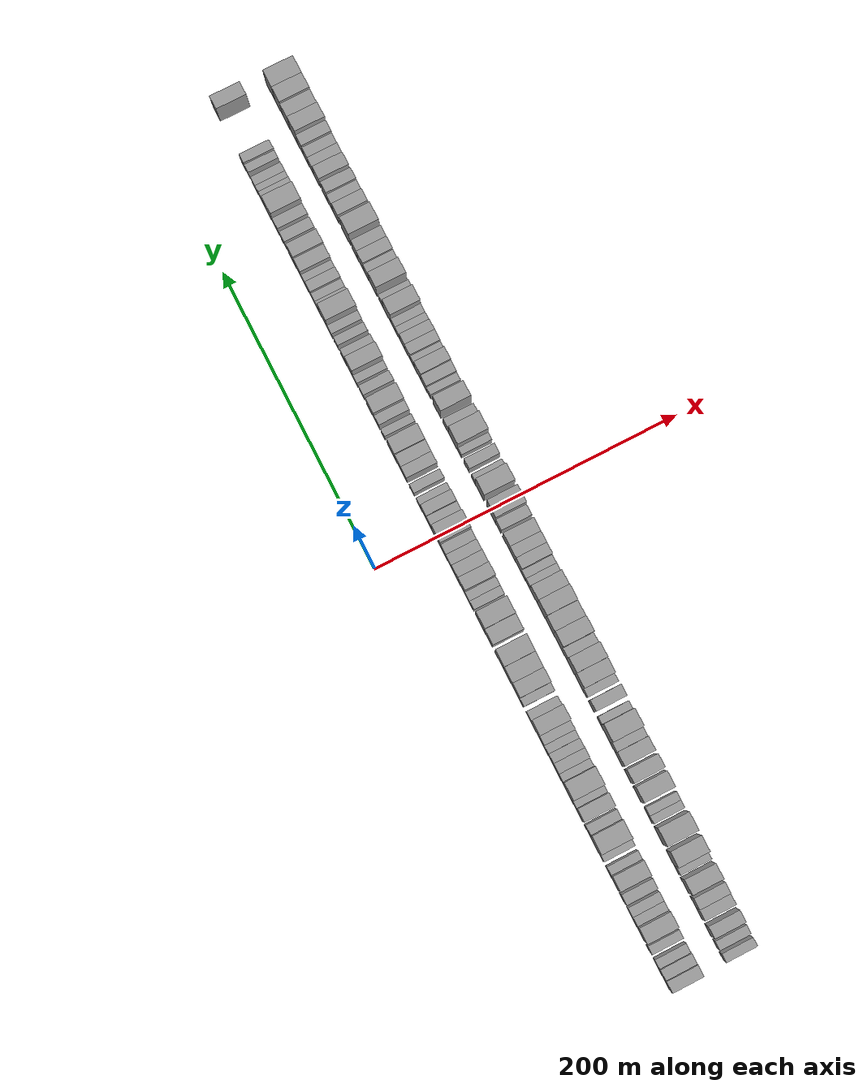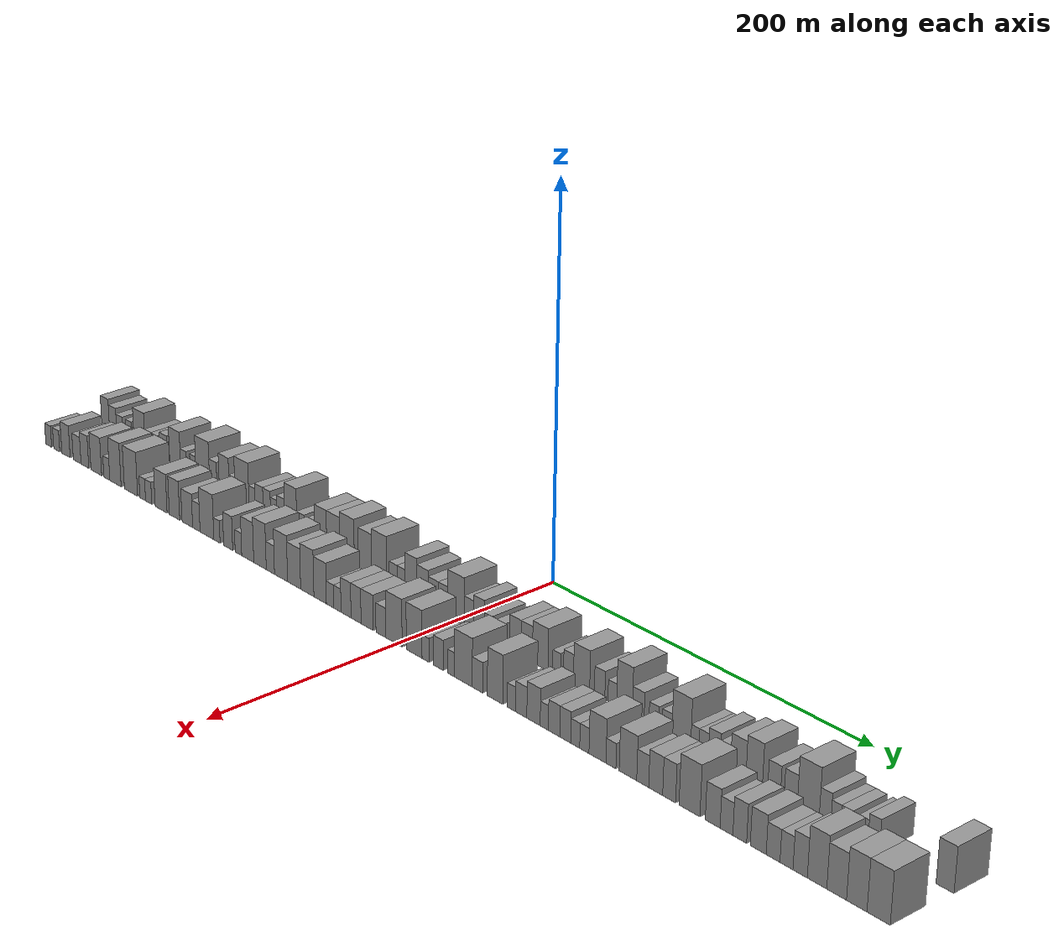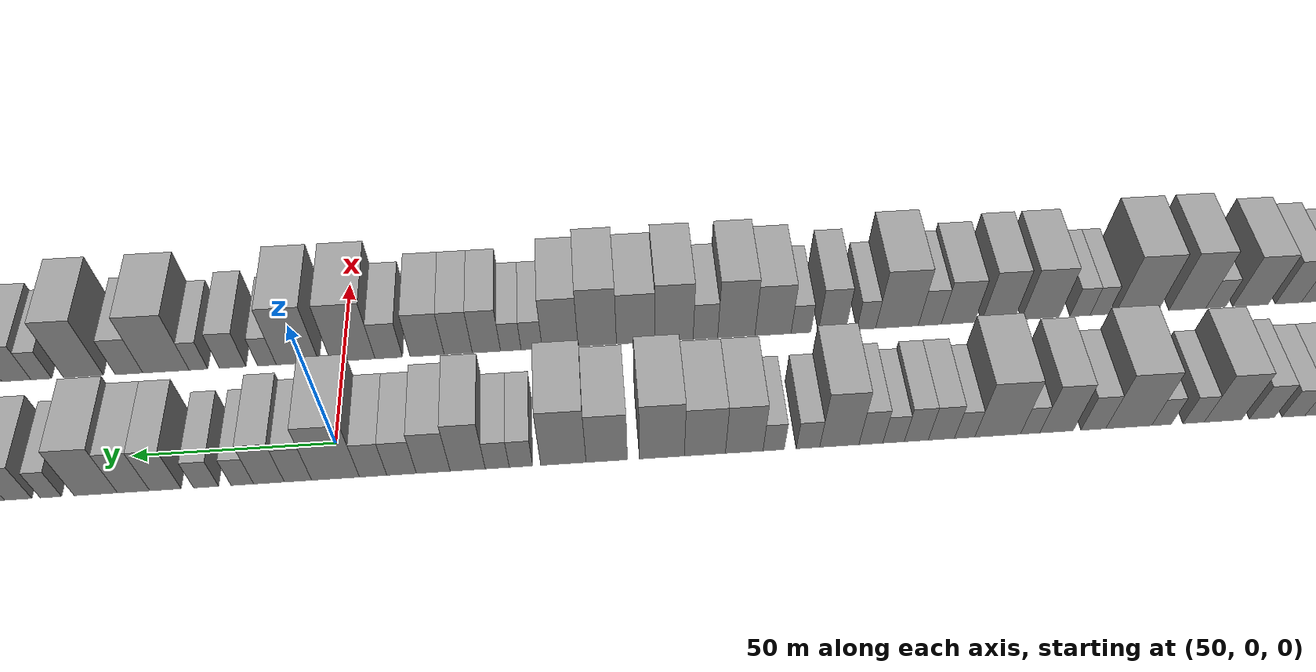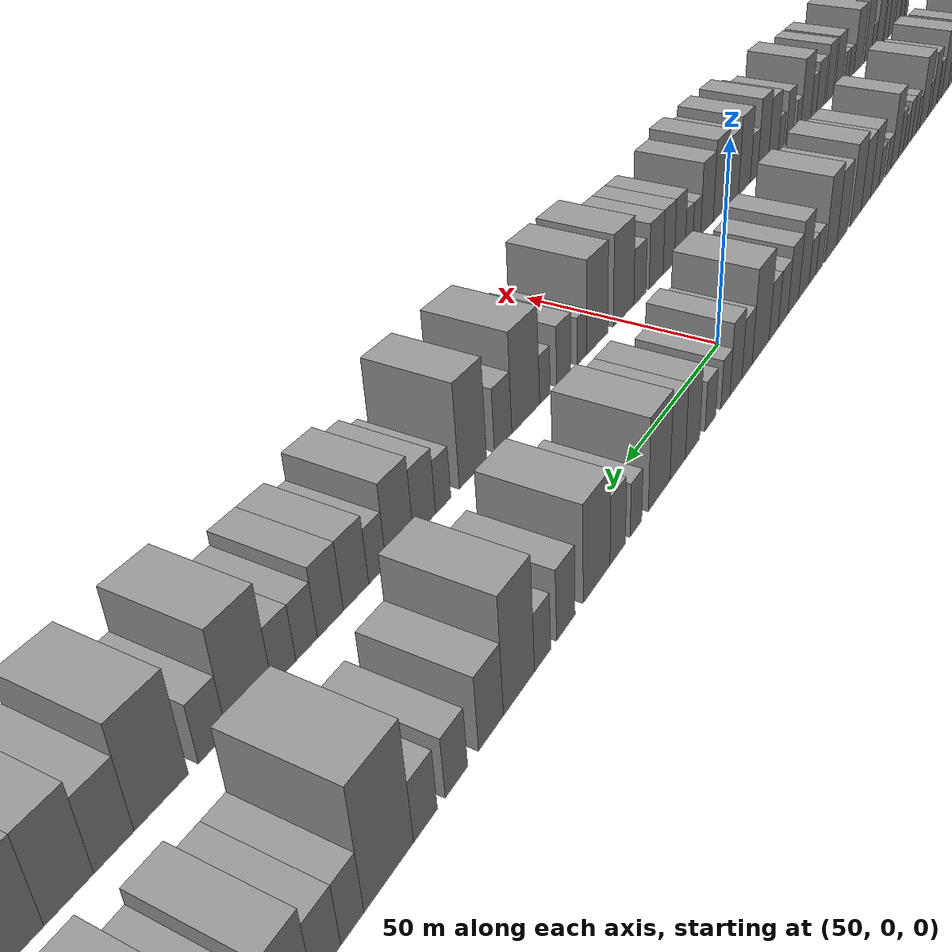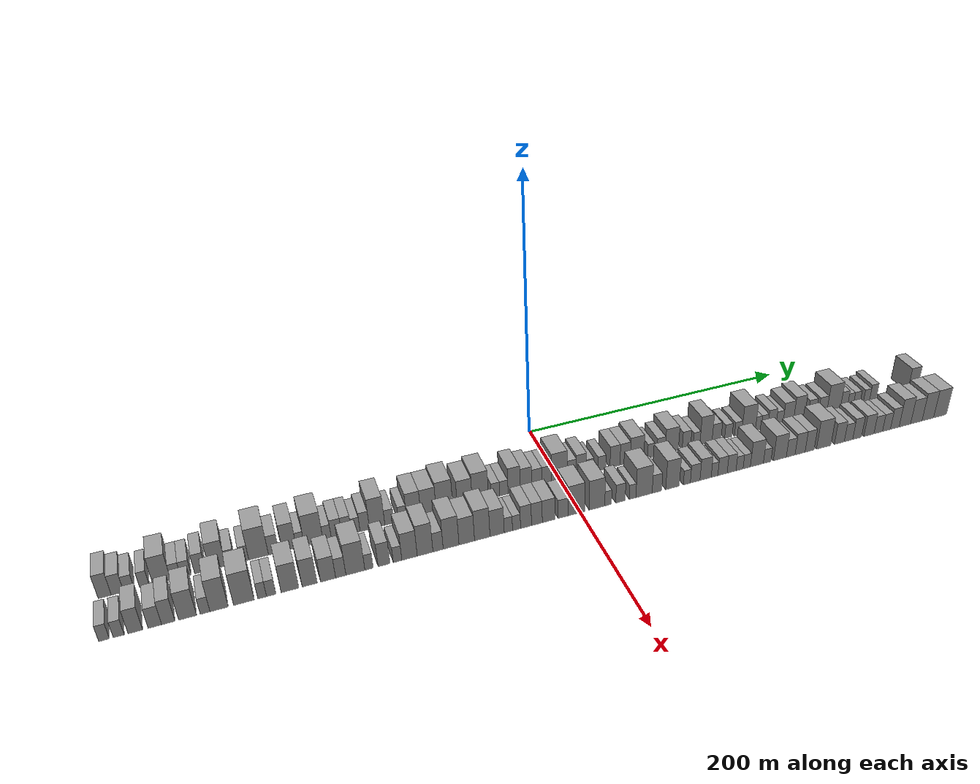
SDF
<sdf version="1.6">
 <world name="default">
  <scene>
   <sky><clouds><speed>12</speed></clouds></sky>
   <ambient>0.4 0.4 0.4 1</ambient>
   <background>0.7 0.7 0.7 1</background>
   <shadows>1</shadows>
  </scene>
  <gravity>0 0 -9.8066</gravity>
  <magnetic_field>6e-06 2.3e-05 -4.2e-05</magnetic_field>
  <physics default="0" name="default_physics" type="ode">
   <ode>
    <solver>
     <type>quick</type>
     <iters>10</iters>
     <sor>1.0</sor>
     <use_dynamic_moi_rescaling>0</use_dynamic_moi_rescaling>
    </solver>
    <constraints>
     <cfm>0</cfm>
     <erp>0.2</erp>
     <contact_max_correcting_vel>100</contact_max_correcting_vel>
     <contact_surface_layer>0.001</contact_surface_layer>
    </constraints>
   </ode>
   <max_step_size>0.004</max_step_size>
   <real_time_factor>1</real_time_factor>
   <real_time_update_rate>250</real_time_update_rate>
  </physics>
  <light name="sun" type="directional">
   <pose>0 0 10 0 0 0</pose>
   <diffuse>0.8 0.8 0.8 1</diffuse>
   <specular>0.2 0.2 0.2 1</specular>
   <attenuation>
    <range>1000</range>
    <constant>0.9</constant>
    <linear>0.01</linear>
    <quadratic>0.001</quadratic>
   </attenuation>
   <direction>-0.5 0.1 -0.9</direction>
  </light>
  <model name="building_1">
   <static>1</static>
   <pose>50.0000 -286.3895 0 0.000000 0.000000 0.000000</pose>
   <link name="link">
    <pose>0 0 9.00 0 0 0</pose>
    <collision name="collision"><geometry><box><size>20.0000 7.2210 18.0000</size></box></geometry></collision>
    <visual name="visual">
     <cast_shadows>0</cast_shadows>
     <geometry><box><size>20.0000 7.2210 18.0000</size></box></geometry>
     <material>
      <script>
       <uri>model://grey_wall/materials/scripts</uri>
       <uri>model://grey_wall/materials/textures</uri>
       <name>vrc/grey_wall</name>
      </script>
     </material>
    </visual>
   </link>
  </model>
  <model name="building_2">
   <static>1</static>
   <pose>50.0000 -279.3729 0 0.000000 0.000000 0.000000</pose>
   <link name="link">
    <pose>0 0 7.50 0 0 0</pose>
    <collision name="collision"><geometry><box><size>20.0000 6.8122 15.0000</size></box></geometry></collision>
    <visual name="visual">
     <cast_shadows>0</cast_shadows>
     <geometry><box><size>20.0000 6.8122 15.0000</size></box></geometry>
     <material>
      <script>
       <uri>model://grey_wall/materials/scripts</uri>
       <uri>model://grey_wall/materials/textures</uri>
       <name>vrc/grey_wall</name>
      </script>
     </material>
    </visual>
   </link>
  </model>
  <model name="building_3">
   <static>1</static>
   <pose>50.0000 -273.0551 0 0.000000 0.000000 0.000000</pose>
   <link name="link">
    <pose>0 0 6.00 0 0 0</pose>
    <collision name="collision"><geometry><box><size>20.0000 5.8235 12.0000</size></box></geometry></collision>
    <visual name="visual">
     <cast_shadows>0</cast_shadows>
     <geometry><box><size>20.0000 5.8235 12.0000</size></box></geometry>
     <material>
      <script>
       <uri>model://grey_wall/materials/scripts</uri>
       <uri>model://grey_wall/materials/textures</uri>
       <name>vrc/grey_wall</name>
      </script>
     </material>
    </visual>
   </link>
  </model>
  <model name="building_4">
   <static>1</static>
   <pose>50.0000 -264.4733 0 0.000000 0.000000 0.000000</pose>
   <link name="link">
    <pose>0 0 6.00 0 0 0</pose>
    <collision name="collision"><geometry><box><size>20.0000 5.3401 12.0000</size></box></geometry></collision>
    <visual name="visual">
     <cast_shadows>0</cast_shadows>
     <geometry><box><size>20.0000 5.3401 12.0000</size></box></geometry>
     <material>
      <script>
       <uri>model://grey_wall/materials/scripts</uri>
       <uri>model://grey_wall/materials/textures</uri>
       <name>vrc/grey_wall</name>
      </script>
     </material>
    </visual>
   </link>
  </model>
  <model name="building_5">
   <static>1</static>
   <pose>50.0000 -254.7529 0 0.000000 0.000000 0.000000</pose>
   <link name="link">
    <pose>0 0 10.50 0 0 0</pose>
    <collision name="collision"><geometry><box><size>20.0000 10.1005 21.0000</size></box></geometry></collision>
    <visual name="visual">
     <cast_shadows>0</cast_shadows>
     <geometry><box><size>20.0000 10.1005 21.0000</size></box></geometry>
     <material>
      <script>
       <uri>model://grey_wall/materials/scripts</uri>
       <uri>model://grey_wall/materials/textures</uri>
       <name>vrc/grey_wall</name>
      </script>
     </material>
    </visual>
   </link>
  </model>
  <model name="building_6">
   <static>1</static>
   <pose>50.0000 -246.8271 0 0.000000 0.000000 0.000000</pose>
   <link name="link">
    <pose>0 0 6.00 0 0 0</pose>
    <collision name="collision"><geometry><box><size>20.0000 5.7511 12.0000</size></box></geometry></collision>
    <visual name="visual">
     <cast_shadows>0</cast_shadows>
     <geometry><box><size>20.0000 5.7511 12.0000</size></box></geometry>
     <material>
      <script>
       <uri>model://grey_wall/materials/scripts</uri>
       <uri>model://grey_wall/materials/textures</uri>
       <name>vrc/grey_wall</name>
      </script>
     </material>
    </visual>
   </link>
  </model>
  <model name="building_7">
   <static>1</static>
   <pose>50.0000 -240.9666 0 0.000000 0.000000 0.000000</pose>
   <link name="link">
    <pose>0 0 6.00 0 0 0</pose>
    <collision name="collision"><geometry><box><size>20.0000 5.9700 12.0000</size></box></geometry></collision>
    <visual name="visual">
     <cast_shadows>0</cast_shadows>
     <geometry><box><size>20.0000 5.9700 12.0000</size></box></geometry>
     <material>
      <script>
       <uri>model://grey_wall/materials/scripts</uri>
       <uri>model://grey_wall/materials/textures</uri>
       <name>vrc/grey_wall</name>
      </script>
     </material>
    </visual>
   </link>
  </model>
  <model name="building_8">
   <static>1</static>
   <pose>50.0000 -232.7494 0 0.000000 0.000000 0.000000</pose>
   <link name="link">
    <pose>0 0 7.50 0 0 0</pose>
    <collision name="collision"><geometry><box><size>20.0000 6.4645 15.0000</size></box></geometry></collision>
    <visual name="visual">
     <cast_shadows>0</cast_shadows>
     <geometry><box><size>20.0000 6.4645 15.0000</size></box></geometry>
     <material>
      <script>
       <uri>model://grey_wall/materials/scripts</uri>
       <uri>model://grey_wall/materials/textures</uri>
       <name>vrc/grey_wall</name>
      </script>
     </material>
    </visual>
   </link>
  </model>
  <model name="building_9">
   <static>1</static>
   <pose>50.0000 -222.6896 0 0.000000 0.000000 0.000000</pose>
   <link name="link">
    <pose>0 0 10.50 0 0 0</pose>
    <collision name="collision"><geometry><box><size>20.0000 9.6550 21.0000</size></box></geometry></collision>
    <visual name="visual">
     <cast_shadows>0</cast_shadows>
     <geometry><box><size>20.0000 9.6550 21.0000</size></box></geometry>
     <material>
      <script>
       <uri>model://grey_wall/materials/scripts</uri>
       <uri>model://grey_wall/materials/textures</uri>
       <name>vrc/grey_wall</name>
      </script>
     </material>
    </visual>
   </link>
  </model>
  <model name="building_10">
   <static>1</static>
   <pose>50.0000 -215.1177 0 0.000000 0.000000 0.000000</pose>
   <link name="link">
    <pose>0 0 6.00 0 0 0</pose>
    <collision name="collision"><geometry><box><size>20.0000 5.4889 12.0000</size></box></geometry></collision>
    <visual name="visual">
     <cast_shadows>0</cast_shadows>
     <geometry><box><size>20.0000 5.4889 12.0000</size></box></geometry>
     <material>
      <script>
       <uri>model://grey_wall/materials/scripts</uri>
       <uri>model://grey_wall/materials/textures</uri>
       <name>vrc/grey_wall</name>
      </script>
     </material>
    </visual>
   </link>
  </model>
  <model name="building_11">
   <static>1</static>
   <pose>50.0000 -206.8450 0 0.000000 0.000000 0.000000</pose>
   <link name="link">
    <pose>0 0 6.00 0 0 0</pose>
    <collision name="collision"><geometry><box><size>20.0000 5.0564 12.0000</size></box></geometry></collision>
    <visual name="visual">
     <cast_shadows>0</cast_shadows>
     <geometry><box><size>20.0000 5.0564 12.0000</size></box></geometry>
     <material>
      <script>
       <uri>model://grey_wall/materials/scripts</uri>
       <uri>model://grey_wall/materials/textures</uri>
       <name>vrc/grey_wall</name>
      </script>
     </material>
    </visual>
   </link>
  </model>
  <model name="building_12">
   <static>1</static>
   <pose>50.0000 -198.4325 0 0.000000 0.000000 0.000000</pose>
   <link name="link">
    <pose>0 0 12.00 0 0 0</pose>
    <collision name="collision"><geometry><box><size>20.0000 11.7688 24.0000</size></box></geometry></collision>
    <visual name="visual">
     <cast_shadows>0</cast_shadows>
     <geometry><box><size>20.0000 11.7688 24.0000</size></box></geometry>
     <material>
      <script>
       <uri>model://grey_wall/materials/scripts</uri>
       <uri>model://grey_wall/materials/textures</uri>
       <name>vrc/grey_wall</name>
      </script>
     </material>
    </visual>
   </link>
  </model>
  <model name="building_13">
   <static>1</static>
   <pose>50.0000 -189.3701 0 0.000000 0.000000 0.000000</pose>
   <link name="link">
    <pose>0 0 7.50 0 0 0</pose>
    <collision name="collision"><geometry><box><size>20.0000 6.3559 15.0000</size></box></geometry></collision>
    <visual name="visual">
     <cast_shadows>0</cast_shadows>
     <geometry><box><size>20.0000 6.3559 15.0000</size></box></geometry>
     <material>
      <script>
       <uri>model://grey_wall/materials/scripts</uri>
       <uri>model://grey_wall/materials/textures</uri>
       <name>vrc/grey_wall</name>
      </script>
     </material>
    </visual>
   </link>
  </model>
  <model name="building_14">
   <static>1</static>
   <pose>50.0000 -179.9469 0 0.000000 0.000000 0.000000</pose>
   <link name="link">
    <pose>0 0 10.50 0 0 0</pose>
    <collision name="collision"><geometry><box><size>20.0000 8.4906 21.0000</size></box></geometry></collision>
    <visual name="visual">
     <cast_shadows>0</cast_shadows>
     <geometry><box><size>20.0000 8.4906 21.0000</size></box></geometry>
     <material>
      <script>
       <uri>model://grey_wall/materials/scripts</uri>
       <uri>model://grey_wall/materials/textures</uri>
       <name>vrc/grey_wall</name>
      </script>
     </material>
    </visual>
   </link>
  </model>
  <model name="building_15">
   <static>1</static>
   <pose>50.0000 -173.2191 0 0.000000 0.000000 0.000000</pose>
   <link name="link">
    <pose>0 0 6.00 0 0 0</pose>
    <collision name="collision"><geometry><box><size>20.0000 4.9650 12.0000</size></box></geometry></collision>
    <visual name="visual">
     <cast_shadows>0</cast_shadows>
     <geometry><box><size>20.0000 4.9650 12.0000</size></box></geometry>
     <material>
      <script>
       <uri>model://grey_wall/materials/scripts</uri>
       <uri>model://grey_wall/materials/textures</uri>
       <name>vrc/grey_wall</name>
      </script>
     </material>
    </visual>
   </link>
  </model>
  <model name="building_16">
   <static>1</static>
   <pose>50.0000 -164.9299 0 0.000000 0.000000 0.000000</pose>
   <link name="link">
    <pose>0 0 12.00 0 0 0</pose>
    <collision name="collision"><geometry><box><size>20.0000 11.6135 24.0000</size></box></geometry></collision>
    <visual name="visual">
     <cast_shadows>0</cast_shadows>
     <geometry><box><size>20.0000 11.6135 24.0000</size></box></geometry>
     <material>
      <script>
       <uri>model://grey_wall/materials/scripts</uri>
       <uri>model://grey_wall/materials/textures</uri>
       <name>vrc/grey_wall</name>
      </script>
     </material>
    </visual>
   </link>
  </model>
  <model name="building_17">
   <static>1</static>
   <pose>50.0000 -156.5490 0 0.000000 0.000000 0.000000</pose>
   <link name="link">
    <pose>0 0 6.00 0 0 0</pose>
    <collision name="collision"><geometry><box><size>20.0000 5.1484 12.0000</size></box></geometry></collision>
    <visual name="visual">
     <cast_shadows>0</cast_shadows>
     <geometry><box><size>20.0000 5.1484 12.0000</size></box></geometry>
     <material>
      <script>
       <uri>model://grey_wall/materials/scripts</uri>
       <uri>model://grey_wall/materials/textures</uri>
       <name>vrc/grey_wall</name>
      </script>
     </material>
    </visual>
   </link>
  </model>
  <model name="building_18">
   <static>1</static>
   <pose>50.0000 -150.6503 0 0.000000 0.000000 0.000000</pose>
   <link name="link">
    <pose>0 0 7.50 0 0 0</pose>
    <collision name="collision"><geometry><box><size>20.0000 6.6490 15.0000</size></box></geometry></collision>
    <visual name="visual">
     <cast_shadows>0</cast_shadows>
     <geometry><box><size>20.0000 6.6490 15.0000</size></box></geometry>
     <material>
      <script>
       <uri>model://grey_wall/materials/scripts</uri>
       <uri>model://grey_wall/materials/textures</uri>
       <name>vrc/grey_wall</name>
      </script>
     </material>
    </visual>
   </link>
  </model>
  <model name="building_19">
   <static>1</static>
   <pose>50.0000 -144.2925 0 0.000000 0.000000 0.000000</pose>
   <link name="link">
    <pose>0 0 7.50 0 0 0</pose>
    <collision name="collision"><geometry><box><size>20.0000 6.0666 15.0000</size></box></geometry></collision>
    <visual name="visual">
     <cast_shadows>0</cast_shadows>
     <geometry><box><size>20.0000 6.0666 15.0000</size></box></geometry>
     <material>
      <script>
       <uri>model://grey_wall/materials/scripts</uri>
       <uri>model://grey_wall/materials/textures</uri>
       <name>vrc/grey_wall</name>
      </script>
     </material>
    </visual>
   </link>
  </model>
  <model name="building_20">
   <static>1</static>
   <pose>50.0000 -138.5595 0 0.000000 0.000000 0.000000</pose>
   <link name="link">
    <pose>0 0 6.00 0 0 0</pose>
    <collision name="collision"><geometry><box><size>20.0000 5.3994 12.0000</size></box></geometry></collision>
    <visual name="visual">
     <cast_shadows>0</cast_shadows>
     <geometry><box><size>20.0000 5.3994 12.0000</size></box></geometry>
     <material>
      <script>
       <uri>model://grey_wall/materials/scripts</uri>
       <uri>model://grey_wall/materials/textures</uri>
       <name>vrc/grey_wall</name>
      </script>
     </material>
    </visual>
   </link>
  </model>
  <model name="building_21">
   <static>1</static>
   <pose>50.0000 -132.8455 0 0.000000 0.000000 0.000000</pose>
   <link name="link">
    <pose>0 0 7.50 0 0 0</pose>
    <collision name="collision"><geometry><box><size>20.0000 6.0286 15.0000</size></box></geometry></collision>
    <visual name="visual">
     <cast_shadows>0</cast_shadows>
     <geometry><box><size>20.0000 6.0286 15.0000</size></box></geometry>
     <material>
      <script>
       <uri>model://grey_wall/materials/scripts</uri>
       <uri>model://grey_wall/materials/textures</uri>
       <name>vrc/grey_wall</name>
      </script>
     </material>
    </visual>
   </link>
  </model>
  <model name="building_22">
   <static>1</static>
   <pose>50.0000 -124.9020 0 0.000000 0.000000 0.000000</pose>
   <link name="link">
    <pose>0 0 12.00 0 0 0</pose>
    <collision name="collision"><geometry><box><size>20.0000 9.8583 24.0000</size></box></geometry></collision>
    <visual name="visual">
     <cast_shadows>0</cast_shadows>
     <geometry><box><size>20.0000 9.8583 24.0000</size></box></geometry>
     <material>
      <script>
       <uri>model://grey_wall/materials/scripts</uri>
       <uri>model://grey_wall/materials/textures</uri>
       <name>vrc/grey_wall</name>
      </script>
     </material>
    </visual>
   </link>
  </model>
  <model name="building_23">
   <static>1</static>
   <pose>50.0000 -117.0329 0 0.000000 0.000000 0.000000</pose>
   <link name="link">
    <pose>0 0 6.00 0 0 0</pose>
    <collision name="collision"><geometry><box><size>20.0000 5.8799 12.0000</size></box></geometry></collision>
    <visual name="visual">
     <cast_shadows>0</cast_shadows>
     <geometry><box><size>20.0000 5.8799 12.0000</size></box></geometry>
     <material>
      <script>
       <uri>model://grey_wall/materials/scripts</uri>
       <uri>model://grey_wall/materials/textures</uri>
       <name>vrc/grey_wall</name>
      </script>
     </material>
    </visual>
   </link>
  </model>
  <model name="building_24">
   <static>1</static>
   <pose>50.0000 -108.4351 0 0.000000 0.000000 0.000000</pose>
   <link name="link">
    <pose>0 0 6.00 0 0 0</pose>
    <collision name="collision"><geometry><box><size>20.0000 5.3156 12.0000</size></box></geometry></collision>
    <visual name="visual">
     <cast_shadows>0</cast_shadows>
     <geometry><box><size>20.0000 5.3156 12.0000</size></box></geometry>
     <material>
      <script>
       <uri>model://grey_wall/materials/scripts</uri>
       <uri>model://grey_wall/materials/textures</uri>
       <name>vrc/grey_wall</name>
      </script>
     </material>
    </visual>
   </link>
  </model>
  <model name="building_25">
   <static>1</static>
   <pose>50.0000 -101.0850 0 0.000000 0.000000 0.000000</pose>
   <link name="link">
    <pose>0 0 10.50 0 0 0</pose>
    <collision name="collision"><geometry><box><size>20.0000 9.3847 21.0000</size></box></geometry></collision>
    <visual name="visual">
     <cast_shadows>0</cast_shadows>
     <geometry><box><size>20.0000 9.3847 21.0000</size></box></geometry>
     <material>
      <script>
       <uri>model://grey_wall/materials/scripts</uri>
       <uri>model://grey_wall/materials/textures</uri>
       <name>vrc/grey_wall</name>
      </script>
     </material>
    </visual>
   </link>
  </model>
  <model name="building_26">
   <static>1</static>
   <pose>50.0000 -91.2807 0 0.000000 0.000000 0.000000</pose>
   <link name="link">
    <pose>0 0 10.50 0 0 0</pose>
    <collision name="collision"><geometry><box><size>20.0000 10.2239 21.0000</size></box></geometry></collision>
    <visual name="visual">
     <cast_shadows>0</cast_shadows>
     <geometry><box><size>20.0000 10.2239 21.0000</size></box></geometry>
     <material>
      <script>
       <uri>model://grey_wall/materials/scripts</uri>
       <uri>model://grey_wall/materials/textures</uri>
       <name>vrc/grey_wall</name>
      </script>
     </material>
    </visual>
   </link>
  </model>
  <model name="building_27">
   <static>1</static>
   <pose>50.0000 -80.6186 0 0.000000 0.000000 0.000000</pose>
   <link name="link">
    <pose>0 0 12.00 0 0 0</pose>
    <collision name="collision"><geometry><box><size>20.0000 11.1003 24.0000</size></box></geometry></collision>
    <visual name="visual">
     <cast_shadows>0</cast_shadows>
     <geometry><box><size>20.0000 11.1003 24.0000</size></box></geometry>
     <material>
      <script>
       <uri>model://grey_wall/materials/scripts</uri>
       <uri>model://grey_wall/materials/textures</uri>
       <name>vrc/grey_wall</name>
      </script>
     </material>
    </visual>
   </link>
  </model>
  <model name="building_28">
   <static>1</static>
   <pose>50.0000 -66.9657 0 0.000000 0.000000 0.000000</pose>
   <link name="link">
    <pose>0 0 10.50 0 0 0</pose>
    <collision name="collision"><geometry><box><size>20.0000 10.2054 21.0000</size></box></geometry></collision>
    <visual name="visual">
     <cast_shadows>0</cast_shadows>
     <geometry><box><size>20.0000 10.2054 21.0000</size></box></geometry>
     <material>
      <script>
       <uri>model://grey_wall/materials/scripts</uri>
       <uri>model://grey_wall/materials/textures</uri>
       <name>vrc/grey_wall</name>
      </script>
     </material>
    </visual>
   </link>
  </model>
  <model name="building_29">
   <static>1</static>
   <pose>50.0000 -56.2812 0 0.000000 0.000000 0.000000</pose>
   <link name="link">
    <pose>0 0 12.00 0 0 0</pose>
    <collision name="collision"><geometry><box><size>20.0000 11.1637 24.0000</size></box></geometry></collision>
    <visual name="visual">
     <cast_shadows>0</cast_shadows>
     <geometry><box><size>20.0000 11.1637 24.0000</size></box></geometry>
     <material>
      <script>
       <uri>model://grey_wall/materials/scripts</uri>
       <uri>model://grey_wall/materials/textures</uri>
       <name>vrc/grey_wall</name>
      </script>
     </material>
    </visual>
   </link>
  </model>
  <model name="building_30">
   <static>1</static>
   <pose>50.0000 -45.8224 0 0.000000 0.000000 0.000000</pose>
   <link name="link">
    <pose>0 0 6.00 0 0 0</pose>
    <collision name="collision"><geometry><box><size>20.0000 5.7540 12.0000</size></box></geometry></collision>
    <visual name="visual">
     <cast_shadows>0</cast_shadows>
     <geometry><box><size>20.0000 5.7540 12.0000</size></box></geometry>
     <material>
      <script>
       <uri>model://grey_wall/materials/scripts</uri>
       <uri>model://grey_wall/materials/textures</uri>
       <name>vrc/grey_wall</name>
      </script>
     </material>
    </visual>
   </link>
  </model>
  <model name="building_31">
   <static>1</static>
   <pose>50.0000 -40.0100 0 0.000000 0.000000 0.000000</pose>
   <link name="link">
    <pose>0 0 6.00 0 0 0</pose>
    <collision name="collision"><geometry><box><size>20.0000 5.8707 12.0000</size></box></geometry></collision>
    <visual name="visual">
     <cast_shadows>0</cast_shadows>
     <geometry><box><size>20.0000 5.8707 12.0000</size></box></geometry>
     <material>
      <script>
       <uri>model://grey_wall/materials/scripts</uri>
       <uri>model://grey_wall/materials/textures</uri>
       <name>vrc/grey_wall</name>
      </script>
     </material>
    </visual>
   </link>
  </model>
  <model name="building_32">
   <static>1</static>
   <pose>50.0000 -32.7911 0 0.000000 0.000000 0.000000</pose>
   <link name="link">
    <pose>0 0 10.50 0 0 0</pose>
    <collision name="collision"><geometry><box><size>20.0000 8.5672 21.0000</size></box></geometry></collision>
    <visual name="visual">
     <cast_shadows>0</cast_shadows>
     <geometry><box><size>20.0000 8.5672 21.0000</size></box></geometry>
     <material>
      <script>
       <uri>model://grey_wall/materials/scripts</uri>
       <uri>model://grey_wall/materials/textures</uri>
       <name>vrc/grey_wall</name>
      </script>
     </material>
    </visual>
   </link>
  </model>
  <model name="building_33">
   <static>1</static>
   <pose>50.0000 -24.3727 0 0.000000 0.000000 0.000000</pose>
   <link name="link">
    <pose>0 0 9.00 0 0 0</pose>
    <collision name="collision"><geometry><box><size>20.0000 8.2696 18.0000</size></box></geometry></collision>
    <visual name="visual">
     <cast_shadows>0</cast_shadows>
     <geometry><box><size>20.0000 8.2696 18.0000</size></box></geometry>
     <material>
      <script>
       <uri>model://grey_wall/materials/scripts</uri>
       <uri>model://grey_wall/materials/textures</uri>
       <name>vrc/grey_wall</name>
      </script>
     </material>
    </visual>
   </link>
  </model>
  <model name="building_34">
   <static>1</static>
   <pose>50.0000 -16.6368 0 0.000000 0.000000 0.000000</pose>
   <link name="link">
    <pose>0 0 7.50 0 0 0</pose>
    <collision name="collision"><geometry><box><size>20.0000 7.2022 15.0000</size></box></geometry></collision>
    <visual name="visual">
     <cast_shadows>0</cast_shadows>
     <geometry><box><size>20.0000 7.2022 15.0000</size></box></geometry>
     <material>
      <script>
       <uri>model://grey_wall/materials/scripts</uri>
       <uri>model://grey_wall/materials/textures</uri>
       <name>vrc/grey_wall</name>
      </script>
     </material>
    </visual>
   </link>
  </model>
  <model name="building_35">
   <static>1</static>
   <pose>50.0000 -9.7083 0 0.000000 0.000000 0.000000</pose>
   <link name="link">
    <pose>0 0 7.50 0 0 0</pose>
    <collision name="collision"><geometry><box><size>20.0000 6.6549 15.0000</size></box></geometry></collision>
    <visual name="visual">
     <cast_shadows>0</cast_shadows>
     <geometry><box><size>20.0000 6.6549 15.0000</size></box></geometry>
     <material>
      <script>
       <uri>model://grey_wall/materials/scripts</uri>
       <uri>model://grey_wall/materials/textures</uri>
       <name>vrc/grey_wall</name>
      </script>
     </material>
    </visual>
   </link>
  </model>
  <model name="building_36">
   <static>1</static>
   <pose>50.0000 -0.5965 0 0.000000 0.000000 0.000000</pose>
   <link name="link">
    <pose>0 0 12.00 0 0 0</pose>
    <collision name="collision"><geometry><box><size>20.0000 11.5688 24.0000</size></box></geometry></collision>
    <visual name="visual">
     <cast_shadows>0</cast_shadows>
     <geometry><box><size>20.0000 11.5688 24.0000</size></box></geometry>
     <material>
      <script>
       <uri>model://grey_wall/materials/scripts</uri>
       <uri>model://grey_wall/materials/textures</uri>
       <name>vrc/grey_wall</name>
      </script>
     </material>
    </visual>
   </link>
  </model>
  <model name="building_37">
   <static>1</static>
   <pose>50.0000 8.4967 0 0.000000 0.000000 0.000000</pose>
   <link name="link">
    <pose>0 0 7.50 0 0 0</pose>
    <collision name="collision"><geometry><box><size>20.0000 6.6175 15.0000</size></box></geometry></collision>
    <visual name="visual">
     <cast_shadows>0</cast_shadows>
     <geometry><box><size>20.0000 6.6175 15.0000</size></box></geometry>
     <material>
      <script>
       <uri>model://grey_wall/materials/scripts</uri>
       <uri>model://grey_wall/materials/textures</uri>
       <name>vrc/grey_wall</name>
      </script>
     </material>
    </visual>
   </link>
  </model>
  <model name="building_38">
   <static>1</static>
   <pose>50.0000 15.5070 0 0.000000 0.000000 0.000000</pose>
   <link name="link">
    <pose>0 0 9.00 0 0 0</pose>
    <collision name="collision"><geometry><box><size>20.0000 7.4033 18.0000</size></box></geometry></collision>
    <visual name="visual">
     <cast_shadows>0</cast_shadows>
     <geometry><box><size>20.0000 7.4033 18.0000</size></box></geometry>
     <material>
      <script>
       <uri>model://grey_wall/materials/scripts</uri>
       <uri>model://grey_wall/materials/textures</uri>
       <name>vrc/grey_wall</name>
      </script>
     </material>
    </visual>
   </link>
  </model>
  <model name="building_39">
   <static>1</static>
   <pose>50.0000 21.9332 0 0.000000 0.000000 0.000000</pose>
   <link name="link">
    <pose>0 0 6.00 0 0 0</pose>
    <collision name="collision"><geometry><box><size>20.0000 5.4490 12.0000</size></box></geometry></collision>
    <visual name="visual">
     <cast_shadows>0</cast_shadows>
     <geometry><box><size>20.0000 5.4490 12.0000</size></box></geometry>
     <material>
      <script>
       <uri>model://grey_wall/materials/scripts</uri>
       <uri>model://grey_wall/materials/textures</uri>
       <name>vrc/grey_wall</name>
      </script>
     </material>
    </visual>
   </link>
  </model>
  <model name="building_40">
   <static>1</static>
   <pose>50.0000 30.6515 0 0.000000 0.000000 0.000000</pose>
   <link name="link">
    <pose>0 0 6.00 0 0 0</pose>
    <collision name="collision"><geometry><box><size>20.0000 5.9877 12.0000</size></box></geometry></collision>
    <visual name="visual">
     <cast_shadows>0</cast_shadows>
     <geometry><box><size>20.0000 5.9877 12.0000</size></box></geometry>
     <material>
      <script>
       <uri>model://grey_wall/materials/scripts</uri>
       <uri>model://grey_wall/materials/textures</uri>
       <name>vrc/grey_wall</name>
      </script>
     </material>
    </visual>
   </link>
  </model>
  <model name="building_41">
   <static>1</static>
   <pose>50.0000 40.4001 0 0.000000 0.000000 0.000000</pose>
   <link name="link">
    <pose>0 0 9.00 0 0 0</pose>
    <collision name="collision"><geometry><box><size>20.0000 7.5096 18.0000</size></box></geometry></collision>
    <visual name="visual">
     <cast_shadows>0</cast_shadows>
     <geometry><box><size>20.0000 7.5096 18.0000</size></box></geometry>
     <material>
      <script>
       <uri>model://grey_wall/materials/scripts</uri>
       <uri>model://grey_wall/materials/textures</uri>
       <name>vrc/grey_wall</name>
      </script>
     </material>
    </visual>
   </link>
  </model>
  <model name="building_42">
   <static>1</static>
   <pose>50.0000 48.0204 0 0.000000 0.000000 0.000000</pose>
   <link name="link">
    <pose>0 0 9.00 0 0 0</pose>
    <collision name="collision"><geometry><box><size>20.0000 7.7310 18.0000</size></box></geometry></collision>
    <visual name="visual">
     <cast_shadows>0</cast_shadows>
     <geometry><box><size>20.0000 7.7310 18.0000</size></box></geometry>
     <material>
      <script>
       <uri>model://grey_wall/materials/scripts</uri>
       <uri>model://grey_wall/materials/textures</uri>
       <name>vrc/grey_wall</name>
      </script>
     </material>
    </visual>
   </link>
  </model>
  <model name="building_43">
   <static>1</static>
   <pose>50.0000 57.0423 0 0.000000 0.000000 0.000000</pose>
   <link name="link">
    <pose>0 0 10.50 0 0 0</pose>
    <collision name="collision"><geometry><box><size>20.0000 10.3128 21.0000</size></box></geometry></collision>
    <visual name="visual">
     <cast_shadows>0</cast_shadows>
     <geometry><box><size>20.0000 10.3128 21.0000</size></box></geometry>
     <material>
      <script>
       <uri>model://grey_wall/materials/scripts</uri>
       <uri>model://grey_wall/materials/textures</uri>
       <name>vrc/grey_wall</name>
      </script>
     </material>
    </visual>
   </link>
  </model>
  <model name="building_44">
   <static>1</static>
   <pose>50.0000 67.7351 0 0.000000 0.000000 0.000000</pose>
   <link name="link">
    <pose>0 0 6.00 0 0 0</pose>
    <collision name="collision"><geometry><box><size>20.0000 5.0728 12.0000</size></box></geometry></collision>
    <visual name="visual">
     <cast_shadows>0</cast_shadows>
     <geometry><box><size>20.0000 5.0728 12.0000</size></box></geometry>
     <material>
      <script>
       <uri>model://grey_wall/materials/scripts</uri>
       <uri>model://grey_wall/materials/textures</uri>
       <name>vrc/grey_wall</name>
      </script>
     </material>
    </visual>
   </link>
  </model>
  <model name="building_45">
   <static>1</static>
   <pose>50.0000 75.4985 0 0.000000 0.000000 0.000000</pose>
   <link name="link">
    <pose>0 0 7.50 0 0 0</pose>
    <collision name="collision"><geometry><box><size>20.0000 6.4539 15.0000</size></box></geometry></collision>
    <visual name="visual">
     <cast_shadows>0</cast_shadows>
     <geometry><box><size>20.0000 6.4539 15.0000</size></box></geometry>
     <material>
      <script>
       <uri>model://grey_wall/materials/scripts</uri>
       <uri>model://grey_wall/materials/textures</uri>
       <name>vrc/grey_wall</name>
      </script>
     </material>
    </visual>
   </link>
  </model>
  <model name="building_46">
   <static>1</static>
   <pose>50.0000 83.9208 0 0.000000 0.000000 0.000000</pose>
   <link name="link">
    <pose>0 0 10.50 0 0 0</pose>
    <collision name="collision"><geometry><box><size>20.0000 10.3909 21.0000</size></box></geometry></collision>
    <visual name="visual">
     <cast_shadows>0</cast_shadows>
     <geometry><box><size>20.0000 10.3909 21.0000</size></box></geometry>
     <material>
      <script>
       <uri>model://grey_wall/materials/scripts</uri>
       <uri>model://grey_wall/materials/textures</uri>
       <name>vrc/grey_wall</name>
      </script>
     </material>
    </visual>
   </link>
  </model>
  <model name="building_47">
   <static>1</static>
   <pose>50.0000 95.4158 0 0.000000 0.000000 0.000000</pose>
   <link name="link">
    <pose>0 0 7.50 0 0 0</pose>
    <collision name="collision"><geometry><box><size>20.0000 6.5991 15.0000</size></box></geometry></collision>
    <visual name="visual">
     <cast_shadows>0</cast_shadows>
     <geometry><box><size>20.0000 6.5991 15.0000</size></box></geometry>
     <material>
      <script>
       <uri>model://grey_wall/materials/scripts</uri>
       <uri>model://grey_wall/materials/textures</uri>
       <name>vrc/grey_wall</name>
      </script>
     </material>
    </visual>
   </link>
  </model>
  <model name="building_48">
   <static>1</static>
   <pose>50.0000 103.4176 0 0.000000 0.000000 0.000000</pose>
   <link name="link">
    <pose>0 0 6.00 0 0 0</pose>
    <collision name="collision"><geometry><box><size>20.0000 5.4044 12.0000</size></box></geometry></collision>
    <visual name="visual">
     <cast_shadows>0</cast_shadows>
     <geometry><box><size>20.0000 5.4044 12.0000</size></box></geometry>
     <material>
      <script>
       <uri>model://grey_wall/materials/scripts</uri>
       <uri>model://grey_wall/materials/textures</uri>
       <name>vrc/grey_wall</name>
      </script>
     </material>
    </visual>
   </link>
  </model>
  <model name="building_49">
   <static>1</static>
   <pose>50.0000 110.9824 0 0.000000 0.000000 0.000000</pose>
   <link name="link">
    <pose>0 0 12.00 0 0 0</pose>
    <collision name="collision"><geometry><box><size>20.0000 9.7251 24.0000</size></box></geometry></collision>
    <visual name="visual">
     <cast_shadows>0</cast_shadows>
     <geometry><box><size>20.0000 9.7251 24.0000</size></box></geometry>
     <material>
      <script>
       <uri>model://grey_wall/materials/scripts</uri>
       <uri>model://grey_wall/materials/textures</uri>
       <name>vrc/grey_wall</name>
      </script>
     </material>
    </visual>
   </link>
  </model>
  <model name="building_50">
   <static>1</static>
   <pose>50.0000 119.4757 0 0.000000 0.000000 0.000000</pose>
   <link name="link">
    <pose>0 0 7.50 0 0 0</pose>
    <collision name="collision"><geometry><box><size>20.0000 7.2615 15.0000</size></box></geometry></collision>
    <visual name="visual">
     <cast_shadows>0</cast_shadows>
     <geometry><box><size>20.0000 7.2615 15.0000</size></box></geometry>
     <material>
      <script>
       <uri>model://grey_wall/materials/scripts</uri>
       <uri>model://grey_wall/materials/textures</uri>
       <name>vrc/grey_wall</name>
      </script>
     </material>
    </visual>
   </link>
  </model>
  <model name="building_51">
   <static>1</static>
   <pose>50.0000 129.0980 0 0.000000 0.000000 0.000000</pose>
   <link name="link">
    <pose>0 0 6.00 0 0 0</pose>
    <collision name="collision"><geometry><box><size>20.0000 5.9830 12.0000</size></box></geometry></collision>
    <visual name="visual">
     <cast_shadows>0</cast_shadows>
     <geometry><box><size>20.0000 5.9830 12.0000</size></box></geometry>
     <material>
      <script>
       <uri>model://grey_wall/materials/scripts</uri>
       <uri>model://grey_wall/materials/textures</uri>
       <name>vrc/grey_wall</name>
      </script>
     </material>
    </visual>
   </link>
  </model>
  <model name="building_52">
   <static>1</static>
   <pose>50.0000 137.0280 0 0.000000 0.000000 0.000000</pose>
   <link name="link">
    <pose>0 0 6.00 0 0 0</pose>
    <collision name="collision"><geometry><box><size>20.0000 5.8771 12.0000</size></box></geometry></collision>
    <visual name="visual">
     <cast_shadows>0</cast_shadows>
     <geometry><box><size>20.0000 5.8771 12.0000</size></box></geometry>
     <material>
      <script>
       <uri>model://grey_wall/materials/scripts</uri>
       <uri>model://grey_wall/materials/textures</uri>
       <name>vrc/grey_wall</name>
      </script>
     </material>
    </visual>
   </link>
  </model>
  <model name="building_53">
   <static>1</static>
   <pose>50.0000 145.5949 0 0.000000 0.000000 0.000000</pose>
   <link name="link">
    <pose>0 0 12.00 0 0 0</pose>
    <collision name="collision"><geometry><box><size>20.0000 11.2568 24.0000</size></box></geometry></collision>
    <visual name="visual">
     <cast_shadows>0</cast_shadows>
     <geometry><box><size>20.0000 11.2568 24.0000</size></box></geometry>
     <material>
      <script>
       <uri>model://grey_wall/materials/scripts</uri>
       <uri>model://grey_wall/materials/textures</uri>
       <name>vrc/grey_wall</name>
      </script>
     </material>
    </visual>
   </link>
  </model>
  <model name="building_54">
   <static>1</static>
   <pose>50.0000 153.6471 0 0.000000 0.000000 0.000000</pose>
   <link name="link">
    <pose>0 0 6.00 0 0 0</pose>
    <collision name="collision"><geometry><box><size>20.0000 4.8477 12.0000</size></box></geometry></collision>
    <visual name="visual">
     <cast_shadows>0</cast_shadows>
     <geometry><box><size>20.0000 4.8477 12.0000</size></box></geometry>
     <material>
      <script>
       <uri>model://grey_wall/materials/scripts</uri>
       <uri>model://grey_wall/materials/textures</uri>
       <name>vrc/grey_wall</name>
      </script>
     </material>
    </visual>
   </link>
  </model>
  <model name="building_55">
   <static>1</static>
   <pose>50.0000 158.8419 0 0.000000 0.000000 0.000000</pose>
   <link name="link">
    <pose>0 0 6.00 0 0 0</pose>
    <collision name="collision"><geometry><box><size>20.0000 5.5418 12.0000</size></box></geometry></collision>
    <visual name="visual">
     <cast_shadows>0</cast_shadows>
     <geometry><box><size>20.0000 5.5418 12.0000</size></box></geometry>
     <material>
      <script>
       <uri>model://grey_wall/materials/scripts</uri>
       <uri>model://grey_wall/materials/textures</uri>
       <name>vrc/grey_wall</name>
      </script>
     </material>
    </visual>
   </link>
  </model>
  <model name="building_56">
   <static>1</static>
   <pose>50.0000 165.1013 0 0.000000 0.000000 0.000000</pose>
   <link name="link">
    <pose>0 0 7.50 0 0 0</pose>
    <collision name="collision"><geometry><box><size>20.0000 6.9770 15.0000</size></box></geometry></collision>
    <visual name="visual">
     <cast_shadows>0</cast_shadows>
     <geometry><box><size>20.0000 6.9770 15.0000</size></box></geometry>
     <material>
      <script>
       <uri>model://grey_wall/materials/scripts</uri>
       <uri>model://grey_wall/materials/textures</uri>
       <name>vrc/grey_wall</name>
      </script>
     </material>
    </visual>
   </link>
  </model>
  <model name="building_57">
   <static>1</static>
   <pose>50.0000 171.5074 0 0.000000 0.000000 0.000000</pose>
   <link name="link">
    <pose>0 0 6.00 0 0 0</pose>
    <collision name="collision"><geometry><box><size>20.0000 5.8352 12.0000</size></box></geometry></collision>
    <visual name="visual">
     <cast_shadows>0</cast_shadows>
     <geometry><box><size>20.0000 5.8352 12.0000</size></box></geometry>
     <material>
      <script>
       <uri>model://grey_wall/materials/scripts</uri>
       <uri>model://grey_wall/materials/textures</uri>
       <name>vrc/grey_wall</name>
      </script>
     </material>
    </visual>
   </link>
  </model>
  <model name="building_58">
   <static>1</static>
   <pose>50.0000 178.8829 0 0.000000 0.000000 0.000000</pose>
   <link name="link">
    <pose>0 0 9.00 0 0 0</pose>
    <collision name="collision"><geometry><box><size>20.0000 8.9159 18.0000</size></box></geometry></collision>
    <visual name="visual">
     <cast_shadows>0</cast_shadows>
     <geometry><box><size>20.0000 8.9159 18.0000</size></box></geometry>
     <material>
      <script>
       <uri>model://grey_wall/materials/scripts</uri>
       <uri>model://grey_wall/materials/textures</uri>
       <name>vrc/grey_wall</name>
      </script>
     </material>
    </visual>
   </link>
  </model>
  <model name="building_59">
   <static>1</static>
   <pose>50.0000 187.9936 0 0.000000 0.000000 0.000000</pose>
   <link name="link">
    <pose>0 0 10.50 0 0 0</pose>
    <collision name="collision"><geometry><box><size>20.0000 9.3054 21.0000</size></box></geometry></collision>
    <visual name="visual">
     <cast_shadows>0</cast_shadows>
     <geometry><box><size>20.0000 9.3054 21.0000</size></box></geometry>
     <material>
      <script>
       <uri>model://grey_wall/materials/scripts</uri>
       <uri>model://grey_wall/materials/textures</uri>
       <name>vrc/grey_wall</name>
      </script>
     </material>
    </visual>
   </link>
  </model>
  <model name="building_60">
   <static>1</static>
   <pose>50.0000 199.2032 0 0.000000 0.000000 0.000000</pose>
   <link name="link">
    <pose>0 0 7.50 0 0 0</pose>
    <collision name="collision"><geometry><box><size>20.0000 7.1140 15.0000</size></box></geometry></collision>
    <visual name="visual">
     <cast_shadows>0</cast_shadows>
     <geometry><box><size>20.0000 7.1140 15.0000</size></box></geometry>
     <material>
      <script>
       <uri>model://grey_wall/materials/scripts</uri>
       <uri>model://grey_wall/materials/textures</uri>
       <name>vrc/grey_wall</name>
      </script>
     </material>
    </visual>
   </link>
  </model>
  <model name="building_61">
   <static>1</static>
   <pose>50.0000 208.4197 0 0.000000 0.000000 0.000000</pose>
   <link name="link">
    <pose>0 0 7.50 0 0 0</pose>
    <collision name="collision"><geometry><box><size>20.0000 7.3190 15.0000</size></box></geometry></collision>
    <visual name="visual">
     <cast_shadows>0</cast_shadows>
     <geometry><box><size>20.0000 7.3190 15.0000</size></box></geometry>
     <material>
      <script>
       <uri>model://grey_wall/materials/scripts</uri>
       <uri>model://grey_wall/materials/textures</uri>
       <name>vrc/grey_wall</name>
      </script>
     </material>
    </visual>
   </link>
  </model>
  <model name="building_62">
   <static>1</static>
   <pose>50.0000 218.0599 0 0.000000 0.000000 0.000000</pose>
   <link name="link">
    <pose>0 0 12.00 0 0 0</pose>
    <collision name="collision"><geometry><box><size>20.0000 11.9614 24.0000</size></box></geometry></collision>
    <visual name="visual">
     <cast_shadows>0</cast_shadows>
     <geometry><box><size>20.0000 11.9614 24.0000</size></box></geometry>
     <material>
      <script>
       <uri>model://grey_wall/materials/scripts</uri>
       <uri>model://grey_wall/materials/textures</uri>
       <name>vrc/grey_wall</name>
      </script>
     </material>
    </visual>
   </link>
  </model>
  <model name="building_63">
   <static>1</static>
   <pose>50.0000 227.1695 0 0.000000 0.000000 0.000000</pose>
   <link name="link">
    <pose>0 0 7.50 0 0 0</pose>
    <collision name="collision"><geometry><box><size>20.0000 6.2578 15.0000</size></box></geometry></collision>
    <visual name="visual">
     <cast_shadows>0</cast_shadows>
     <geometry><box><size>20.0000 6.2578 15.0000</size></box></geometry>
     <material>
      <script>
       <uri>model://grey_wall/materials/scripts</uri>
       <uri>model://grey_wall/materials/textures</uri>
       <name>vrc/grey_wall</name>
      </script>
     </material>
    </visual>
   </link>
  </model>
  <model name="building_64">
   <static>1</static>
   <pose>50.0000 232.8984 0 0.000000 0.000000 0.000000</pose>
   <link name="link">
    <pose>0 0 6.00 0 0 0</pose>
    <collision name="collision"><geometry><box><size>20.0000 5.2000 12.0000</size></box></geometry></collision>
    <visual name="visual">
     <cast_shadows>0</cast_shadows>
     <geometry><box><size>20.0000 5.2000 12.0000</size></box></geometry>
     <material>
      <script>
       <uri>model://grey_wall/materials/scripts</uri>
       <uri>model://grey_wall/materials/textures</uri>
       <name>vrc/grey_wall</name>
      </script>
     </material>
    </visual>
   </link>
  </model>
  <model name="building_65">
   <static>1</static>
   <pose>50.0000 238.4969 0 0.000000 0.000000 0.000000</pose>
   <link name="link">
    <pose>0 0 6.00 0 0 0</pose>
    <collision name="collision"><geometry><box><size>20.0000 5.9970 12.0000</size></box></geometry></collision>
    <visual name="visual">
     <cast_shadows>0</cast_shadows>
     <geometry><box><size>20.0000 5.9970 12.0000</size></box></geometry>
     <material>
      <script>
       <uri>model://grey_wall/materials/scripts</uri>
       <uri>model://grey_wall/materials/textures</uri>
       <name>vrc/grey_wall</name>
      </script>
     </material>
    </visual>
   </link>
  </model>
  <model name="building_66">
   <static>1</static>
   <pose>50.0000 247.2121 0 0.000000 0.000000 0.000000</pose>
   <link name="link">
    <pose>0 0 6.00 0 0 0</pose>
    <collision name="collision"><geometry><box><size>20.0000 5.4335 12.0000</size></box></geometry></collision>
    <visual name="visual">
     <cast_shadows>0</cast_shadows>
     <geometry><box><size>20.0000 5.4335 12.0000</size></box></geometry>
     <material>
      <script>
       <uri>model://grey_wall/materials/scripts</uri>
       <uri>model://grey_wall/materials/textures</uri>
       <name>vrc/grey_wall</name>
      </script>
     </material>
    </visual>
   </link>
  </model>
  <model name="building_67">
   <static>1</static>
   <pose>50.0000 252.9840 0 0.000000 0.000000 0.000000</pose>
   <link name="link">
    <pose>0 0 7.50 0 0 0</pose>
    <collision name="collision"><geometry><box><size>20.0000 6.1104 15.0000</size></box></geometry></collision>
    <visual name="visual">
     <cast_shadows>0</cast_shadows>
     <geometry><box><size>20.0000 6.1104 15.0000</size></box></geometry>
     <material>
      <script>
       <uri>model://grey_wall/materials/scripts</uri>
       <uri>model://grey_wall/materials/textures</uri>
       <name>vrc/grey_wall</name>
      </script>
     </material>
    </visual>
   </link>
  </model>
  <model name="building_68">
   <static>1</static>
   <pose>50.0000 289.4859 0 0.000000 0.000000 0.000000</pose>
   <link name="link">
    <pose>0 0 10.50 0 0 0</pose>
    <collision name="collision"><geometry><box><size>20.0000 8.9645 21.0000</size></box></geometry></collision>
    <visual name="visual">
     <cast_shadows>0</cast_shadows>
     <geometry><box><size>20.0000 8.9645 21.0000</size></box></geometry>
     <material>
      <script>
       <uri>model://grey_wall/materials/scripts</uri>
       <uri>model://grey_wall/materials/textures</uri>
       <name>vrc/grey_wall</name>
      </script>
     </material>
    </visual>
   </link>
  </model>
  <model name="building_69">
   <static>1</static>
   <pose>85.0000 -287.2218 0 0.000000 0.000000 0.000000</pose>
   <link name="link">
    <pose>0 0 6.00 0 0 0</pose>
    <collision name="collision"><geometry><box><size>20.0000 5.5563 12.0000</size></box></geometry></collision>
    <visual name="visual">
     <cast_shadows>0</cast_shadows>
     <geometry><box><size>20.0000 5.5563 12.0000</size></box></geometry>
     <material>
      <script>
       <uri>model://grey_wall/materials/scripts</uri>
       <uri>model://grey_wall/materials/textures</uri>
       <name>vrc/grey_wall</name>
      </script>
     </material>
    </visual>
   </link>
  </model>
  <model name="building_70">
   <static>1</static>
   <pose>85.0000 -279.5764 0 0.000000 0.000000 0.000000</pose>
   <link name="link">
    <pose>0 0 6.00 0 0 0</pose>
    <collision name="collision"><geometry><box><size>20.0000 5.7345 12.0000</size></box></geometry></collision>
    <visual name="visual">
     <cast_shadows>0</cast_shadows>
     <geometry><box><size>20.0000 5.7345 12.0000</size></box></geometry>
     <material>
      <script>
       <uri>model://grey_wall/materials/scripts</uri>
       <uri>model://grey_wall/materials/textures</uri>
       <name>vrc/grey_wall</name>
      </script>
     </material>
    </visual>
   </link>
  </model>
  <model name="building_71">
   <static>1</static>
   <pose>85.0000 -270.8508 0 0.000000 0.000000 0.000000</pose>
   <link name="link">
    <pose>0 0 9.00 0 0 0</pose>
    <collision name="collision"><geometry><box><size>20.0000 7.7169 18.0000</size></box></geometry></collision>
    <visual name="visual">
     <cast_shadows>0</cast_shadows>
     <geometry><box><size>20.0000 7.7169 18.0000</size></box></geometry>
     <material>
      <script>
       <uri>model://grey_wall/materials/scripts</uri>
       <uri>model://grey_wall/materials/textures</uri>
       <name>vrc/grey_wall</name>
      </script>
     </material>
    </visual>
   </link>
  </model>
  <model name="building_72">
   <static>1</static>
   <pose>85.0000 -260.3975 0 0.000000 0.000000 0.000000</pose>
   <link name="link">
    <pose>0 0 7.50 0 0 0</pose>
    <collision name="collision"><geometry><box><size>20.0000 7.1897 15.0000</size></box></geometry></collision>
    <visual name="visual">
     <cast_shadows>0</cast_shadows>
     <geometry><box><size>20.0000 7.1897 15.0000</size></box></geometry>
     <material>
      <script>
       <uri>model://grey_wall/materials/scripts</uri>
       <uri>model://grey_wall/materials/textures</uri>
       <name>vrc/grey_wall</name>
      </script>
     </material>
    </visual>
   </link>
  </model>
  <model name="building_73">
   <static>1</static>
   <pose>85.0000 -253.2020 0 0.000000 0.000000 0.000000</pose>
   <link name="link">
    <pose>0 0 9.00 0 0 0</pose>
    <collision name="collision"><geometry><box><size>20.0000 7.2012 18.0000</size></box></geometry></collision>
    <visual name="visual">
     <cast_shadows>0</cast_shadows>
     <geometry><box><size>20.0000 7.2012 18.0000</size></box></geometry>
     <material>
      <script>
       <uri>model://grey_wall/materials/scripts</uri>
       <uri>model://grey_wall/materials/textures</uri>
       <name>vrc/grey_wall</name>
      </script>
     </material>
    </visual>
   </link>
  </model>
  <model name="building_74">
   <static>1</static>
   <pose>85.0000 -242.7041 0 0.000000 0.000000 0.000000</pose>
   <link name="link">
    <pose>0 0 10.50 0 0 0</pose>
    <collision name="collision"><geometry><box><size>20.0000 9.7946 21.0000</size></box></geometry></collision>
    <visual name="visual">
     <cast_shadows>0</cast_shadows>
     <geometry><box><size>20.0000 9.7946 21.0000</size></box></geometry>
     <material>
      <script>
       <uri>model://grey_wall/materials/scripts</uri>
       <uri>model://grey_wall/materials/textures</uri>
       <name>vrc/grey_wall</name>
      </script>
     </material>
    </visual>
   </link>
  </model>
  <model name="building_75">
   <static>1</static>
   <pose>85.0000 -233.1061 0 0.000000 0.000000 0.000000</pose>
   <link name="link">
    <pose>0 0 6.00 0 0 0</pose>
    <collision name="collision"><geometry><box><size>20.0000 5.4014 12.0000</size></box></geometry></collision>
    <visual name="visual">
     <cast_shadows>0</cast_shadows>
     <geometry><box><size>20.0000 5.4014 12.0000</size></box></geometry>
     <material>
      <script>
       <uri>model://grey_wall/materials/scripts</uri>
       <uri>model://grey_wall/materials/textures</uri>
       <name>vrc/grey_wall</name>
      </script>
     </material>
    </visual>
   </link>
  </model>
  <model name="building_76">
   <static>1</static>
   <pose>85.0000 -225.3223 0 0.000000 0.000000 0.000000</pose>
   <link name="link">
    <pose>0 0 12.00 0 0 0</pose>
    <collision name="collision"><geometry><box><size>20.0000 10.1661 24.0000</size></box></geometry></collision>
    <visual name="visual">
     <cast_shadows>0</cast_shadows>
     <geometry><box><size>20.0000 10.1661 24.0000</size></box></geometry>
     <material>
      <script>
       <uri>model://grey_wall/materials/scripts</uri>
       <uri>model://grey_wall/materials/textures</uri>
       <name>vrc/grey_wall</name>
      </script>
     </material>
    </visual>
   </link>
  </model>
  <model name="building_77">
   <static>1</static>
   <pose>85.0000 -211.3919 0 0.000000 0.000000 0.000000</pose>
   <link name="link">
    <pose>0 0 12.00 0 0 0</pose>
    <collision name="collision"><geometry><box><size>20.0000 11.6947 24.0000</size></box></geometry></collision>
    <visual name="visual">
     <cast_shadows>0</cast_shadows>
     <geometry><box><size>20.0000 11.6947 24.0000</size></box></geometry>
     <material>
      <script>
       <uri>model://grey_wall/materials/scripts</uri>
       <uri>model://grey_wall/materials/textures</uri>
       <name>vrc/grey_wall</name>
      </script>
     </material>
    </visual>
   </link>
  </model>
  <model name="building_78">
   <static>1</static>
   <pose>85.0000 -201.0595 0 0.000000 0.000000 0.000000</pose>
   <link name="link">
    <pose>0 0 6.00 0 0 0</pose>
    <collision name="collision"><geometry><box><size>20.0000 4.9701 12.0000</size></box></geometry></collision>
    <visual name="visual">
     <cast_shadows>0</cast_shadows>
     <geometry><box><size>20.0000 4.9701 12.0000</size></box></geometry>
     <material>
      <script>
       <uri>model://grey_wall/materials/scripts</uri>
       <uri>model://grey_wall/materials/textures</uri>
       <name>vrc/grey_wall</name>
      </script>
     </material>
    </visual>
   </link>
  </model>
  <model name="building_79">
   <static>1</static>
   <pose>85.0000 -195.8603 0 0.000000 0.000000 0.000000</pose>
   <link name="link">
    <pose>0 0 6.00 0 0 0</pose>
    <collision name="collision"><geometry><box><size>20.0000 5.4282 12.0000</size></box></geometry></collision>
    <visual name="visual">
     <cast_shadows>0</cast_shadows>
     <geometry><box><size>20.0000 5.4282 12.0000</size></box></geometry>
     <material>
      <script>
       <uri>model://grey_wall/materials/scripts</uri>
       <uri>model://grey_wall/materials/textures</uri>
       <name>vrc/grey_wall</name>
      </script>
     </material>
    </visual>
   </link>
  </model>
  <model name="building_80">
   <static>1</static>
   <pose>85.0000 -185.0249 0 0.000000 0.000000 0.000000</pose>
   <link name="link">
    <pose>0 0 10.50 0 0 0</pose>
    <collision name="collision"><geometry><box><size>20.0000 10.2426 21.0000</size></box></geometry></collision>
    <visual name="visual">
     <cast_shadows>0</cast_shadows>
     <geometry><box><size>20.0000 10.2426 21.0000</size></box></geometry>
     <material>
      <script>
       <uri>model://grey_wall/materials/scripts</uri>
       <uri>model://grey_wall/materials/textures</uri>
       <name>vrc/grey_wall</name>
      </script>
     </material>
    </visual>
   </link>
  </model>
  <model name="building_81">
   <static>1</static>
   <pose>85.0000 -173.4950 0 0.000000 0.000000 0.000000</pose>
   <link name="link">
    <pose>0 0 10.50 0 0 0</pose>
    <collision name="collision"><geometry><box><size>20.0000 8.8173 21.0000</size></box></geometry></collision>
    <visual name="visual">
     <cast_shadows>0</cast_shadows>
     <geometry><box><size>20.0000 8.8173 21.0000</size></box></geometry>
     <material>
      <script>
       <uri>model://grey_wall/materials/scripts</uri>
       <uri>model://grey_wall/materials/textures</uri>
       <name>vrc/grey_wall</name>
      </script>
     </material>
    </visual>
   </link>
  </model>
  <model name="building_82">
   <static>1</static>
   <pose>85.0000 -162.6044 0 0.000000 0.000000 0.000000</pose>
   <link name="link">
    <pose>0 0 9.00 0 0 0</pose>
    <collision name="collision"><geometry><box><size>20.0000 8.9639 18.0000</size></box></geometry></collision>
    <visual name="visual">
     <cast_shadows>0</cast_shadows>
     <geometry><box><size>20.0000 8.9639 18.0000</size></box></geometry>
     <material>
      <script>
       <uri>model://grey_wall/materials/scripts</uri>
       <uri>model://grey_wall/materials/textures</uri>
       <name>vrc/grey_wall</name>
      </script>
     </material>
    </visual>
   </link>
  </model>
  <model name="building_83">
   <static>1</static>
   <pose>85.0000 -155.0308 0 0.000000 0.000000 0.000000</pose>
   <link name="link">
    <pose>0 0 7.50 0 0 0</pose>
    <collision name="collision"><geometry><box><size>20.0000 6.1832 15.0000</size></box></geometry></collision>
    <visual name="visual">
     <cast_shadows>0</cast_shadows>
     <geometry><box><size>20.0000 6.1832 15.0000</size></box></geometry>
     <material>
      <script>
       <uri>model://grey_wall/materials/scripts</uri>
       <uri>model://grey_wall/materials/textures</uri>
       <name>vrc/grey_wall</name>
      </script>
     </material>
    </visual>
   </link>
  </model>
  <model name="building_84">
   <static>1</static>
   <pose>85.0000 -146.2024 0 0.000000 0.000000 0.000000</pose>
   <link name="link">
    <pose>0 0 12.00 0 0 0</pose>
    <collision name="collision"><geometry><box><size>20.0000 11.4736 24.0000</size></box></geometry></collision>
    <visual name="visual">
     <cast_shadows>0</cast_shadows>
     <geometry><box><size>20.0000 11.4736 24.0000</size></box></geometry>
     <material>
      <script>
       <uri>model://grey_wall/materials/scripts</uri>
       <uri>model://grey_wall/materials/textures</uri>
       <name>vrc/grey_wall</name>
      </script>
     </material>
    </visual>
   </link>
  </model>
  <model name="building_85">
   <static>1</static>
   <pose>85.0000 -137.9275 0 0.000000 0.000000 0.000000</pose>
   <link name="link">
    <pose>0 0 6.00 0 0 0</pose>
    <collision name="collision"><geometry><box><size>20.0000 5.0762 12.0000</size></box></geometry></collision>
    <visual name="visual">
     <cast_shadows>0</cast_shadows>
     <geometry><box><size>20.0000 5.0762 12.0000</size></box></geometry>
     <material>
      <script>
       <uri>model://grey_wall/materials/scripts</uri>
       <uri>model://grey_wall/materials/textures</uri>
       <name>vrc/grey_wall</name>
      </script>
     </material>
    </visual>
   </link>
  </model>
  <model name="building_86">
   <static>1</static>
   <pose>85.0000 -128.7155 0 0.000000 0.000000 0.000000</pose>
   <link name="link">
    <pose>0 0 9.00 0 0 0</pose>
    <collision name="collision"><geometry><box><size>20.0000 7.3477 18.0000</size></box></geometry></collision>
    <visual name="visual">
     <cast_shadows>0</cast_shadows>
     <geometry><box><size>20.0000 7.3477 18.0000</size></box></geometry>
     <material>
      <script>
       <uri>model://grey_wall/materials/scripts</uri>
       <uri>model://grey_wall/materials/textures</uri>
       <name>vrc/grey_wall</name>
      </script>
     </material>
    </visual>
   </link>
  </model>
  <model name="building_87">
   <static>1</static>
   <pose>85.0000 -120.3929 0 0.000000 0.000000 0.000000</pose>
   <link name="link">
    <pose>0 0 6.00 0 0 0</pose>
    <collision name="collision"><geometry><box><size>20.0000 5.2977 12.0000</size></box></geometry></collision>
    <visual name="visual">
     <cast_shadows>0</cast_shadows>
     <geometry><box><size>20.0000 5.2977 12.0000</size></box></geometry>
     <material>
      <script>
       <uri>model://grey_wall/materials/scripts</uri>
       <uri>model://grey_wall/materials/textures</uri>
       <name>vrc/grey_wall</name>
      </script>
     </material>
    </visual>
   </link>
  </model>
  <model name="building_88">
   <static>1</static>
   <pose>85.0000 -112.9138 0 0.000000 0.000000 0.000000</pose>
   <link name="link">
    <pose>0 0 10.50 0 0 0</pose>
    <collision name="collision"><geometry><box><size>20.0000 9.6604 21.0000</size></box></geometry></collision>
    <visual name="visual">
     <cast_shadows>0</cast_shadows>
     <geometry><box><size>20.0000 9.6604 21.0000</size></box></geometry>
     <material>
      <script>
       <uri>model://grey_wall/materials/scripts</uri>
       <uri>model://grey_wall/materials/textures</uri>
       <name>vrc/grey_wall</name>
      </script>
     </material>
    </visual>
   </link>
  </model>
  <model name="building_89">
   <static>1</static>
   <pose>85.0000 -103.1183 0 0.000000 0.000000 0.000000</pose>
   <link name="link">
    <pose>0 0 12.00 0 0 0</pose>
    <collision name="collision"><geometry><box><size>20.0000 9.9305 24.0000</size></box></geometry></collision>
    <visual name="visual">
     <cast_shadows>0</cast_shadows>
     <geometry><box><size>20.0000 9.9305 24.0000</size></box></geometry>
     <material>
      <script>
       <uri>model://grey_wall/materials/scripts</uri>
       <uri>model://grey_wall/materials/textures</uri>
       <name>vrc/grey_wall</name>
      </script>
     </material>
    </visual>
   </link>
  </model>
  <model name="building_90">
   <static>1</static>
   <pose>85.0000 -94.8995 0 0.000000 0.000000 0.000000</pose>
   <link name="link">
    <pose>0 0 7.50 0 0 0</pose>
    <collision name="collision"><geometry><box><size>20.0000 6.5071 15.0000</size></box></geometry></collision>
    <visual name="visual">
     <cast_shadows>0</cast_shadows>
     <geometry><box><size>20.0000 6.5071 15.0000</size></box></geometry>
     <material>
      <script>
       <uri>model://grey_wall/materials/scripts</uri>
       <uri>model://grey_wall/materials/textures</uri>
       <name>vrc/grey_wall</name>
      </script>
     </material>
    </visual>
   </link>
  </model>
  <model name="building_91">
   <static>1</static>
   <pose>85.0000 -86.5533 0 0.000000 0.000000 0.000000</pose>
   <link name="link">
    <pose>0 0 12.00 0 0 0</pose>
    <collision name="collision"><geometry><box><size>20.0000 10.1855 24.0000</size></box></geometry></collision>
    <visual name="visual">
     <cast_shadows>0</cast_shadows>
     <geometry><box><size>20.0000 10.1855 24.0000</size></box></geometry>
     <material>
      <script>
       <uri>model://grey_wall/materials/scripts</uri>
       <uri>model://grey_wall/materials/textures</uri>
       <name>vrc/grey_wall</name>
      </script>
     </material>
    </visual>
   </link>
  </model>
  <model name="building_92">
   <static>1</static>
   <pose>85.0000 -76.4142 0 0.000000 0.000000 0.000000</pose>
   <link name="link">
    <pose>0 0 10.50 0 0 0</pose>
    <collision name="collision"><geometry><box><size>20.0000 10.0926 21.0000</size></box></geometry></collision>
    <visual name="visual">
     <cast_shadows>0</cast_shadows>
     <geometry><box><size>20.0000 10.0926 21.0000</size></box></geometry>
     <material>
      <script>
       <uri>model://grey_wall/materials/scripts</uri>
       <uri>model://grey_wall/materials/textures</uri>
       <name>vrc/grey_wall</name>
      </script>
     </material>
    </visual>
   </link>
  </model>
  <model name="building_93">
   <static>1</static>
   <pose>85.0000 -66.3062 0 0.000000 0.000000 0.000000</pose>
   <link name="link">
    <pose>0 0 12.00 0 0 0</pose>
    <collision name="collision"><geometry><box><size>20.0000 10.1236 24.0000</size></box></geometry></collision>
    <visual name="visual">
     <cast_shadows>0</cast_shadows>
     <geometry><box><size>20.0000 10.1236 24.0000</size></box></geometry>
     <material>
      <script>
       <uri>model://grey_wall/materials/scripts</uri>
       <uri>model://grey_wall/materials/textures</uri>
       <name>vrc/grey_wall</name>
      </script>
     </material>
    </visual>
   </link>
  </model>
  <model name="building_94">
   <static>1</static>
   <pose>85.0000 -56.5176 0 0.000000 0.000000 0.000000</pose>
   <link name="link">
    <pose>0 0 10.50 0 0 0</pose>
    <collision name="collision"><geometry><box><size>20.0000 9.4535 21.0000</size></box></geometry></collision>
    <visual name="visual">
     <cast_shadows>0</cast_shadows>
     <geometry><box><size>20.0000 9.4535 21.0000</size></box></geometry>
     <material>
      <script>
       <uri>model://grey_wall/materials/scripts</uri>
       <uri>model://grey_wall/materials/textures</uri>
       <name>vrc/grey_wall</name>
      </script>
     </material>
    </visual>
   </link>
  </model>
  <model name="building_95">
   <static>1</static>
   <pose>85.0000 -49.0352 0 0.000000 0.000000 0.000000</pose>
   <link name="link">
    <pose>0 0 6.00 0 0 0</pose>
    <collision name="collision"><geometry><box><size>20.0000 5.5114 12.0000</size></box></geometry></collision>
    <visual name="visual">
     <cast_shadows>0</cast_shadows>
     <geometry><box><size>20.0000 5.5114 12.0000</size></box></geometry>
     <material>
      <script>
       <uri>model://grey_wall/materials/scripts</uri>
       <uri>model://grey_wall/materials/textures</uri>
       <name>vrc/grey_wall</name>
      </script>
     </material>
    </visual>
   </link>
  </model>
  <model name="building_96">
   <static>1</static>
   <pose>85.0000 -43.5820 0 0.000000 0.000000 0.000000</pose>
   <link name="link">
    <pose>0 0 6.00 0 0 0</pose>
    <collision name="collision"><geometry><box><size>20.0000 5.3950 12.0000</size></box></geometry></collision>
    <visual name="visual">
     <cast_shadows>0</cast_shadows>
     <geometry><box><size>20.0000 5.3950 12.0000</size></box></geometry>
     <material>
      <script>
       <uri>model://grey_wall/materials/scripts</uri>
       <uri>model://grey_wall/materials/textures</uri>
       <name>vrc/grey_wall</name>
      </script>
     </material>
    </visual>
   </link>
  </model>
  <model name="building_97">
   <static>1</static>
   <pose>85.0000 -37.1915 0 0.000000 0.000000 0.000000</pose>
   <link name="link">
    <pose>0 0 9.00 0 0 0</pose>
    <collision name="collision"><geometry><box><size>20.0000 7.3859 18.0000</size></box></geometry></collision>
    <visual name="visual">
     <cast_shadows>0</cast_shadows>
     <geometry><box><size>20.0000 7.3859 18.0000</size></box></geometry>
     <material>
      <script>
       <uri>model://grey_wall/materials/scripts</uri>
       <uri>model://grey_wall/materials/textures</uri>
       <name>vrc/grey_wall</name>
      </script>
     </material>
    </visual>
   </link>
  </model>
  <model name="building_98">
   <static>1</static>
   <pose>85.0000 -29.8182 0 0.000000 0.000000 0.000000</pose>
   <link name="link">
    <pose>0 0 9.00 0 0 0</pose>
    <collision name="collision"><geometry><box><size>20.0000 7.3609 18.0000</size></box></geometry></collision>
    <visual name="visual">
     <cast_shadows>0</cast_shadows>
     <geometry><box><size>20.0000 7.3609 18.0000</size></box></geometry>
     <material>
      <script>
       <uri>model://grey_wall/materials/scripts</uri>
       <uri>model://grey_wall/materials/textures</uri>
       <name>vrc/grey_wall</name>
      </script>
     </material>
    </visual>
   </link>
  </model>
  <model name="building_99">
   <static>1</static>
   <pose>85.0000 -21.7149 0 0.000000 0.000000 0.000000</pose>
   <link name="link">
    <pose>0 0 9.00 0 0 0</pose>
    <collision name="collision"><geometry><box><size>20.0000 8.8457 18.0000</size></box></geometry></collision>
    <visual name="visual">
     <cast_shadows>0</cast_shadows>
     <geometry><box><size>20.0000 8.8457 18.0000</size></box></geometry>
     <material>
      <script>
       <uri>model://grey_wall/materials/scripts</uri>
       <uri>model://grey_wall/materials/textures</uri>
       <name>vrc/grey_wall</name>
      </script>
     </material>
    </visual>
   </link>
  </model>
  <model name="building_100">
   <static>1</static>
   <pose>85.0000 -11.7125 0 0.000000 0.000000 0.000000</pose>
   <link name="link">
    <pose>0 0 7.50 0 0 0</pose>
    <collision name="collision"><geometry><box><size>20.0000 7.1592 15.0000</size></box></geometry></collision>
    <visual name="visual">
     <cast_shadows>0</cast_shadows>
     <geometry><box><size>20.0000 7.1592 15.0000</size></box></geometry>
     <material>
      <script>
       <uri>model://grey_wall/materials/scripts</uri>
       <uri>model://grey_wall/materials/textures</uri>
       <name>vrc/grey_wall</name>
      </script>
     </material>
    </visual>
   </link>
  </model>
  <model name="building_101">
   <static>1</static>
   <pose>85.0000 -2.3817 0 0.000000 0.000000 0.000000</pose>
   <link name="link">
    <pose>0 0 12.00 0 0 0</pose>
    <collision name="collision"><geometry><box><size>20.0000 11.5022 24.0000</size></box></geometry></collision>
    <visual name="visual">
     <cast_shadows>0</cast_shadows>
     <geometry><box><size>20.0000 11.5022 24.0000</size></box></geometry>
     <material>
      <script>
       <uri>model://grey_wall/materials/scripts</uri>
       <uri>model://grey_wall/materials/textures</uri>
       <name>vrc/grey_wall</name>
      </script>
     </material>
    </visual>
   </link>
  </model>
  <model name="building_102">
   <static>1</static>
   <pose>85.0000 11.8843 0 0.000000 0.000000 0.000000</pose>
   <link name="link">
    <pose>0 0 12.00 0 0 0</pose>
    <collision name="collision"><geometry><box><size>20.0000 11.0299 24.0000</size></box></geometry></collision>
    <visual name="visual">
     <cast_shadows>0</cast_shadows>
     <geometry><box><size>20.0000 11.0299 24.0000</size></box></geometry>
     <material>
      <script>
       <uri>model://grey_wall/materials/scripts</uri>
       <uri>model://grey_wall/materials/textures</uri>
       <name>vrc/grey_wall</name>
      </script>
     </material>
    </visual>
   </link>
  </model>
  <model name="building_103">
   <static>1</static>
   <pose>85.0000 19.8069 0 0.000000 0.000000 0.000000</pose>
   <link name="link">
    <pose>0 0 6.00 0 0 0</pose>
    <collision name="collision"><geometry><box><size>20.0000 4.8152 12.0000</size></box></geometry></collision>
    <visual name="visual">
     <cast_shadows>0</cast_shadows>
     <geometry><box><size>20.0000 4.8152 12.0000</size></box></geometry>
     <material>
      <script>
       <uri>model://grey_wall/materials/scripts</uri>
       <uri>model://grey_wall/materials/textures</uri>
       <name>vrc/grey_wall</name>
      </script>
     </material>
    </visual>
   </link>
  </model>
  <model name="building_104">
   <static>1</static>
   <pose>85.0000 28.6116 0 0.000000 0.000000 0.000000</pose>
   <link name="link">
    <pose>0 0 7.50 0 0 0</pose>
    <collision name="collision"><geometry><box><size>20.0000 6.7942 15.0000</size></box></geometry></collision>
    <visual name="visual">
     <cast_shadows>0</cast_shadows>
     <geometry><box><size>20.0000 6.7942 15.0000</size></box></geometry>
     <material>
      <script>
       <uri>model://grey_wall/materials/scripts</uri>
       <uri>model://grey_wall/materials/textures</uri>
       <name>vrc/grey_wall</name>
      </script>
     </material>
    </visual>
   </link>
  </model>
  <model name="building_105">
   <static>1</static>
   <pose>85.0000 37.4100 0 0.000000 0.000000 0.000000</pose>
   <link name="link">
    <pose>0 0 6.00 0 0 0</pose>
    <collision name="collision"><geometry><box><size>20.0000 4.8026 12.0000</size></box></geometry></collision>
    <visual name="visual">
     <cast_shadows>0</cast_shadows>
     <geometry><box><size>20.0000 4.8026 12.0000</size></box></geometry>
     <material>
      <script>
       <uri>model://grey_wall/materials/scripts</uri>
       <uri>model://grey_wall/materials/textures</uri>
       <name>vrc/grey_wall</name>
      </script>
     </material>
    </visual>
   </link>
  </model>
  <model name="building_106">
   <static>1</static>
   <pose>85.0000 45.7350 0 0.000000 0.000000 0.000000</pose>
   <link name="link">
    <pose>0 0 12.00 0 0 0</pose>
    <collision name="collision"><geometry><box><size>20.0000 11.8475 24.0000</size></box></geometry></collision>
    <visual name="visual">
     <cast_shadows>0</cast_shadows>
     <geometry><box><size>20.0000 11.8475 24.0000</size></box></geometry>
     <material>
      <script>
       <uri>model://grey_wall/materials/scripts</uri>
       <uri>model://grey_wall/materials/textures</uri>
       <name>vrc/grey_wall</name>
      </script>
     </material>
    </visual>
   </link>
  </model>
  <model name="building_107">
   <static>1</static>
   <pose>85.0000 55.1727 0 0.000000 0.000000 0.000000</pose>
   <link name="link">
    <pose>0 0 7.50 0 0 0</pose>
    <collision name="collision"><geometry><box><size>20.0000 7.0278 15.0000</size></box></geometry></collision>
    <visual name="visual">
     <cast_shadows>0</cast_shadows>
     <geometry><box><size>20.0000 7.0278 15.0000</size></box></geometry>
     <material>
      <script>
       <uri>model://grey_wall/materials/scripts</uri>
       <uri>model://grey_wall/materials/textures</uri>
       <name>vrc/grey_wall</name>
      </script>
     </material>
    </visual>
   </link>
  </model>
  <model name="building_108">
   <static>1</static>
   <pose>85.0000 66.7685 0 0.000000 0.000000 0.000000</pose>
   <link name="link">
    <pose>0 0 12.00 0 0 0</pose>
    <collision name="collision"><geometry><box><size>20.0000 10.1637 24.0000</size></box></geometry></collision>
    <visual name="visual">
     <cast_shadows>0</cast_shadows>
     <geometry><box><size>20.0000 10.1637 24.0000</size></box></geometry>
     <material>
      <script>
       <uri>model://grey_wall/materials/scripts</uri>
       <uri>model://grey_wall/materials/textures</uri>
       <name>vrc/grey_wall</name>
      </script>
     </material>
    </visual>
   </link>
  </model>
  <model name="building_109">
   <static>1</static>
   <pose>85.0000 77.4833 0 0.000000 0.000000 0.000000</pose>
   <link name="link">
    <pose>0 0 6.00 0 0 0</pose>
    <collision name="collision"><geometry><box><size>20.0000 5.2660 12.0000</size></box></geometry></collision>
    <visual name="visual">
     <cast_shadows>0</cast_shadows>
     <geometry><box><size>20.0000 5.2660 12.0000</size></box></geometry>
     <material>
      <script>
       <uri>model://grey_wall/materials/scripts</uri>
       <uri>model://grey_wall/materials/textures</uri>
       <name>vrc/grey_wall</name>
      </script>
     </material>
    </visual>
   </link>
  </model>
  <model name="building_110">
   <static>1</static>
   <pose>85.0000 83.7670 0 0.000000 0.000000 0.000000</pose>
   <link name="link">
    <pose>0 0 7.50 0 0 0</pose>
    <collision name="collision"><geometry><box><size>20.0000 7.3013 15.0000</size></box></geometry></collision>
    <visual name="visual">
     <cast_shadows>0</cast_shadows>
     <geometry><box><size>20.0000 7.3013 15.0000</size></box></geometry>
     <material>
      <script>
       <uri>model://grey_wall/materials/scripts</uri>
       <uri>model://grey_wall/materials/textures</uri>
       <name>vrc/grey_wall</name>
      </script>
     </material>
    </visual>
   </link>
  </model>
  <model name="building_111">
   <static>1</static>
   <pose>85.0000 91.6896 0 0.000000 0.000000 0.000000</pose>
   <link name="link">
    <pose>0 0 9.00 0 0 0</pose>
    <collision name="collision"><geometry><box><size>20.0000 8.5438 18.0000</size></box></geometry></collision>
    <visual name="visual">
     <cast_shadows>0</cast_shadows>
     <geometry><box><size>20.0000 8.5438 18.0000</size></box></geometry>
     <material>
      <script>
       <uri>model://grey_wall/materials/scripts</uri>
       <uri>model://grey_wall/materials/textures</uri>
       <name>vrc/grey_wall</name>
      </script>
     </material>
    </visual>
   </link>
  </model>
  <model name="building_112">
   <static>1</static>
   <pose>85.0000 98.5437 0 0.000000 0.000000 0.000000</pose>
   <link name="link">
    <pose>0 0 6.00 0 0 0</pose>
    <collision name="collision"><geometry><box><size>20.0000 5.1644 12.0000</size></box></geometry></collision>
    <visual name="visual">
     <cast_shadows>0</cast_shadows>
     <geometry><box><size>20.0000 5.1644 12.0000</size></box></geometry>
     <material>
      <script>
       <uri>model://grey_wall/materials/scripts</uri>
       <uri>model://grey_wall/materials/textures</uri>
       <name>vrc/grey_wall</name>
      </script>
     </material>
    </visual>
   </link>
  </model>
  <model name="building_113">
   <static>1</static>
   <pose>85.0000 104.7234 0 0.000000 0.000000 0.000000</pose>
   <link name="link">
    <pose>0 0 7.50 0 0 0</pose>
    <collision name="collision"><geometry><box><size>20.0000 7.1950 15.0000</size></box></geometry></collision>
    <visual name="visual">
     <cast_shadows>0</cast_shadows>
     <geometry><box><size>20.0000 7.1950 15.0000</size></box></geometry>
     <material>
      <script>
       <uri>model://grey_wall/materials/scripts</uri>
       <uri>model://grey_wall/materials/textures</uri>
       <name>vrc/grey_wall</name>
      </script>
     </material>
    </visual>
   </link>
  </model>
  <model name="building_114">
   <static>1</static>
   <pose>85.0000 111.7532 0 0.000000 0.000000 0.000000</pose>
   <link name="link">
    <pose>0 0 7.50 0 0 0</pose>
    <collision name="collision"><geometry><box><size>20.0000 6.8646 15.0000</size></box></geometry></collision>
    <visual name="visual">
     <cast_shadows>0</cast_shadows>
     <geometry><box><size>20.0000 6.8646 15.0000</size></box></geometry>
     <material>
      <script>
       <uri>model://grey_wall/materials/scripts</uri>
       <uri>model://grey_wall/materials/textures</uri>
       <name>vrc/grey_wall</name>
      </script>
     </material>
    </visual>
   </link>
  </model>
  <model name="building_115">
   <static>1</static>
   <pose>85.0000 117.9529 0 0.000000 0.000000 0.000000</pose>
   <link name="link">
    <pose>0 0 6.00 0 0 0</pose>
    <collision name="collision"><geometry><box><size>20.0000 5.5347 12.0000</size></box></geometry></collision>
    <visual name="visual">
     <cast_shadows>0</cast_shadows>
     <geometry><box><size>20.0000 5.5347 12.0000</size></box></geometry>
     <material>
      <script>
       <uri>model://grey_wall/materials/scripts</uri>
       <uri>model://grey_wall/materials/textures</uri>
       <name>vrc/grey_wall</name>
      </script>
     </material>
    </visual>
   </link>
  </model>
  <model name="building_116">
   <static>1</static>
   <pose>85.0000 123.5769 0 0.000000 0.000000 0.000000</pose>
   <link name="link">
    <pose>0 0 6.00 0 0 0</pose>
    <collision name="collision"><geometry><box><size>20.0000 5.7134 12.0000</size></box></geometry></collision>
    <visual name="visual">
     <cast_shadows>0</cast_shadows>
     <geometry><box><size>20.0000 5.7134 12.0000</size></box></geometry>
     <material>
      <script>
       <uri>model://grey_wall/materials/scripts</uri>
       <uri>model://grey_wall/materials/textures</uri>
       <name>vrc/grey_wall</name>
      </script>
     </material>
    </visual>
   </link>
  </model>
  <model name="building_117">
   <static>1</static>
   <pose>85.0000 131.6043 0 0.000000 0.000000 0.000000</pose>
   <link name="link">
    <pose>0 0 10.50 0 0 0</pose>
    <collision name="collision"><geometry><box><size>20.0000 10.3415 21.0000</size></box></geometry></collision>
    <visual name="visual">
     <cast_shadows>0</cast_shadows>
     <geometry><box><size>20.0000 10.3415 21.0000</size></box></geometry>
     <material>
      <script>
       <uri>model://grey_wall/materials/scripts</uri>
       <uri>model://grey_wall/materials/textures</uri>
       <name>vrc/grey_wall</name>
      </script>
     </material>
    </visual>
   </link>
  </model>
  <model name="building_118">
   <static>1</static>
   <pose>85.0000 139.7650 0 0.000000 0.000000 0.000000</pose>
   <link name="link">
    <pose>0 0 6.00 0 0 0</pose>
    <collision name="collision"><geometry><box><size>20.0000 5.9799 12.0000</size></box></geometry></collision>
    <visual name="visual">
     <cast_shadows>0</cast_shadows>
     <geometry><box><size>20.0000 5.9799 12.0000</size></box></geometry>
     <material>
      <script>
       <uri>model://grey_wall/materials/scripts</uri>
       <uri>model://grey_wall/materials/textures</uri>
       <name>vrc/grey_wall</name>
      </script>
     </material>
    </visual>
   </link>
  </model>
  <model name="building_119">
   <static>1</static>
   <pose>85.0000 149.9678 0 0.000000 0.000000 0.000000</pose>
   <link name="link">
    <pose>0 0 10.50 0 0 0</pose>
    <collision name="collision"><geometry><box><size>20.0000 10.4256 21.0000</size></box></geometry></collision>
    <visual name="visual">
     <cast_shadows>0</cast_shadows>
     <geometry><box><size>20.0000 10.4256 21.0000</size></box></geometry>
     <material>
      <script>
       <uri>model://grey_wall/materials/scripts</uri>
       <uri>model://grey_wall/materials/textures</uri>
       <name>vrc/grey_wall</name>
      </script>
     </material>
    </visual>
   </link>
  </model>
  <model name="building_120">
   <static>1</static>
   <pose>85.0000 158.7238 0 0.000000 0.000000 0.000000</pose>
   <link name="link">
    <pose>0 0 7.50 0 0 0</pose>
    <collision name="collision"><geometry><box><size>20.0000 7.0864 15.0000</size></box></geometry></collision>
    <visual name="visual">
     <cast_shadows>0</cast_shadows>
     <geometry><box><size>20.0000 7.0864 15.0000</size></box></geometry>
     <material>
      <script>
       <uri>model://grey_wall/materials/scripts</uri>
       <uri>model://grey_wall/materials/textures</uri>
       <name>vrc/grey_wall</name>
      </script>
     </material>
    </visual>
   </link>
  </model>
  <model name="building_121">
   <static>1</static>
   <pose>85.0000 166.3435 0 0.000000 0.000000 0.000000</pose>
   <link name="link">
    <pose>0 0 9.00 0 0 0</pose>
    <collision name="collision"><geometry><box><size>20.0000 8.1529 18.0000</size></box></geometry></collision>
    <visual name="visual">
     <cast_shadows>0</cast_shadows>
     <geometry><box><size>20.0000 8.1529 18.0000</size></box></geometry>
     <material>
      <script>
       <uri>model://grey_wall/materials/scripts</uri>
       <uri>model://grey_wall/materials/textures</uri>
       <name>vrc/grey_wall</name>
      </script>
     </material>
    </visual>
   </link>
  </model>
  <model name="building_122">
   <static>1</static>
   <pose>85.0000 174.1622 0 0.000000 0.000000 0.000000</pose>
   <link name="link">
    <pose>0 0 9.00 0 0 0</pose>
    <collision name="collision"><geometry><box><size>20.0000 7.4846 18.0000</size></box></geometry></collision>
    <visual name="visual">
     <cast_shadows>0</cast_shadows>
     <geometry><box><size>20.0000 7.4846 18.0000</size></box></geometry>
     <material>
      <script>
       <uri>model://grey_wall/materials/scripts</uri>
       <uri>model://grey_wall/materials/textures</uri>
       <name>vrc/grey_wall</name>
      </script>
     </material>
    </visual>
   </link>
  </model>
  <model name="building_123">
   <static>1</static>
   <pose>85.0000 185.8533 0 0.000000 0.000000 0.000000</pose>
   <link name="link">
    <pose>0 0 12.00 0 0 0</pose>
    <collision name="collision"><geometry><box><size>20.0000 11.8974 24.0000</size></box></geometry></collision>
    <visual name="visual">
     <cast_shadows>0</cast_shadows>
     <geometry><box><size>20.0000 11.8974 24.0000</size></box></geometry>
     <material>
      <script>
       <uri>model://grey_wall/materials/scripts</uri>
       <uri>model://grey_wall/materials/textures</uri>
       <name>vrc/grey_wall</name>
      </script>
     </material>
    </visual>
   </link>
  </model>
  <model name="building_124">
   <static>1</static>
   <pose>85.0000 198.9534 0 0.000000 0.000000 0.000000</pose>
   <link name="link">
    <pose>0 0 9.00 0 0 0</pose>
    <collision name="collision"><geometry><box><size>20.0000 8.3029 18.0000</size></box></geometry></collision>
    <visual name="visual">
     <cast_shadows>0</cast_shadows>
     <geometry><box><size>20.0000 8.3029 18.0000</size></box></geometry>
     <material>
      <script>
       <uri>model://grey_wall/materials/scripts</uri>
       <uri>model://grey_wall/materials/textures</uri>
       <name>vrc/grey_wall</name>
      </script>
     </material>
    </visual>
   </link>
  </model>
  <model name="building_125">
   <static>1</static>
   <pose>85.0000 206.6556 0 0.000000 0.000000 0.000000</pose>
   <link name="link">
    <pose>0 0 7.50 0 0 0</pose>
    <collision name="collision"><geometry><box><size>20.0000 7.1014 15.0000</size></box></geometry></collision>
    <visual name="visual">
     <cast_shadows>0</cast_shadows>
     <geometry><box><size>20.0000 7.1014 15.0000</size></box></geometry>
     <material>
      <script>
       <uri>model://grey_wall/materials/scripts</uri>
       <uri>model://grey_wall/materials/textures</uri>
       <name>vrc/grey_wall</name>
      </script>
     </material>
    </visual>
   </link>
  </model>
  <model name="building_126">
   <static>1</static>
   <pose>85.0000 213.9838 0 0.000000 0.000000 0.000000</pose>
   <link name="link">
    <pose>0 0 9.00 0 0 0</pose>
    <collision name="collision"><geometry><box><size>20.0000 7.5550 18.0000</size></box></geometry></collision>
    <visual name="visual">
     <cast_shadows>0</cast_shadows>
     <geometry><box><size>20.0000 7.5550 18.0000</size></box></geometry>
     <material>
      <script>
       <uri>model://grey_wall/materials/scripts</uri>
       <uri>model://grey_wall/materials/textures</uri>
       <name>vrc/grey_wall</name>
      </script>
     </material>
    </visual>
   </link>
  </model>
  <model name="building_127">
   <static>1</static>
   <pose>85.0000 224.0881 0 0.000000 0.000000 0.000000</pose>
   <link name="link">
    <pose>0 0 9.00 0 0 0</pose>
    <collision name="collision"><geometry><box><size>20.0000 8.6537 18.0000</size></box></geometry></collision>
    <visual name="visual">
     <cast_shadows>0</cast_shadows>
     <geometry><box><size>20.0000 8.6537 18.0000</size></box></geometry>
     <material>
      <script>
       <uri>model://grey_wall/materials/scripts</uri>
       <uri>model://grey_wall/materials/textures</uri>
       <name>vrc/grey_wall</name>
      </script>
     </material>
    </visual>
   </link>
  </model>
  <model name="building_128">
   <static>1</static>
   <pose>85.0000 232.1134 0 0.000000 0.000000 0.000000</pose>
   <link name="link">
    <pose>0 0 7.50 0 0 0</pose>
    <collision name="collision"><geometry><box><size>20.0000 7.3967 15.0000</size></box></geometry></collision>
    <visual name="visual">
     <cast_shadows>0</cast_shadows>
     <geometry><box><size>20.0000 7.3967 15.0000</size></box></geometry>
     <material>
      <script>
       <uri>model://grey_wall/materials/scripts</uri>
       <uri>model://grey_wall/materials/textures</uri>
       <name>vrc/grey_wall</name>
      </script>
     </material>
    </visual>
   </link>
  </model>
  <model name="building_129">
   <static>1</static>
   <pose>85.0000 239.2734 0 0.000000 0.000000 0.000000</pose>
   <link name="link">
    <pose>0 0 7.50 0 0 0</pose>
    <collision name="collision"><geometry><box><size>20.0000 6.9234 15.0000</size></box></geometry></collision>
    <visual name="visual">
     <cast_shadows>0</cast_shadows>
     <geometry><box><size>20.0000 6.9234 15.0000</size></box></geometry>
     <material>
      <script>
       <uri>model://grey_wall/materials/scripts</uri>
       <uri>model://grey_wall/materials/textures</uri>
       <name>vrc/grey_wall</name>
      </script>
     </material>
    </visual>
   </link>
  </model>
  <model name="building_130">
   <static>1</static>
   <pose>85.0000 246.5230 0 0.000000 0.000000 0.000000</pose>
   <link name="link">
    <pose>0 0 9.00 0 0 0</pose>
    <collision name="collision"><geometry><box><size>20.0000 7.5756 18.0000</size></box></geometry></collision>
    <visual name="visual">
     <cast_shadows>0</cast_shadows>
     <geometry><box><size>20.0000 7.5756 18.0000</size></box></geometry>
     <material>
      <script>
       <uri>model://grey_wall/materials/scripts</uri>
       <uri>model://grey_wall/materials/textures</uri>
       <name>vrc/grey_wall</name>
      </script>
     </material>
    </visual>
   </link>
  </model>
  <model name="building_131">
   <static>1</static>
   <pose>85.0000 255.3901 0 0.000000 0.000000 0.000000</pose>
   <link name="link">
    <pose>0 0 12.00 0 0 0</pose>
    <collision name="collision"><geometry><box><size>20.0000 10.1586 24.0000</size></box></geometry></collision>
    <visual name="visual">
     <cast_shadows>0</cast_shadows>
     <geometry><box><size>20.0000 10.1586 24.0000</size></box></geometry>
     <material>
      <script>
       <uri>model://grey_wall/materials/scripts</uri>
       <uri>model://grey_wall/materials/textures</uri>
       <name>vrc/grey_wall</name>
      </script>
     </material>
    </visual>
   </link>
  </model>
  <model name="building_132">
   <static>1</static>
   <pose>85.0000 265.5498 0 0.000000 0.000000 0.000000</pose>
   <link name="link">
    <pose>0 0 10.50 0 0 0</pose>
    <collision name="collision"><geometry><box><size>20.0000 10.1608 21.0000</size></box></geometry></collision>
    <visual name="visual">
     <cast_shadows>0</cast_shadows>
     <geometry><box><size>20.0000 10.1608 21.0000</size></box></geometry>
     <material>
      <script>
       <uri>model://grey_wall/materials/scripts</uri>
       <uri>model://grey_wall/materials/textures</uri>
       <name>vrc/grey_wall</name>
      </script>
     </material>
    </visual>
   </link>
  </model>
  <model name="building_133">
   <static>1</static>
   <pose>85.0000 275.8265 0 0.000000 0.000000 0.000000</pose>
   <link name="link">
    <pose>0 0 12.00 0 0 0</pose>
    <collision name="collision"><geometry><box><size>20.0000 10.3926 24.0000</size></box></geometry></collision>
    <visual name="visual">
     <cast_shadows>0</cast_shadows>
     <geometry><box><size>20.0000 10.3926 24.0000</size></box></geometry>
     <material>
      <script>
       <uri>model://grey_wall/materials/scripts</uri>
       <uri>model://grey_wall/materials/textures</uri>
       <name>vrc/grey_wall</name>
      </script>
     </material>
    </visual>
   </link>
  </model>
  <model name="building_134">
   <static>1</static>
   <pose>85.0000 286.8474 0 0.000000 0.000000 0.000000</pose>
   <link name="link">
    <pose>0 0 12.00 0 0 0</pose>
    <collision name="collision"><geometry><box><size>20.0000 11.6492 24.0000</size></box></geometry></collision>
    <visual name="visual">
     <cast_shadows>0</cast_shadows>
     <geometry><box><size>20.0000 11.6492 24.0000</size></box></geometry>
     <material>
      <script>
       <uri>model://grey_wall/materials/scripts</uri>
       <uri>model://grey_wall/materials/textures</uri>
       <name>vrc/grey_wall</name>
      </script>
     </material>
    </visual>
   </link>
  </model>
 </world>
</sdf>
